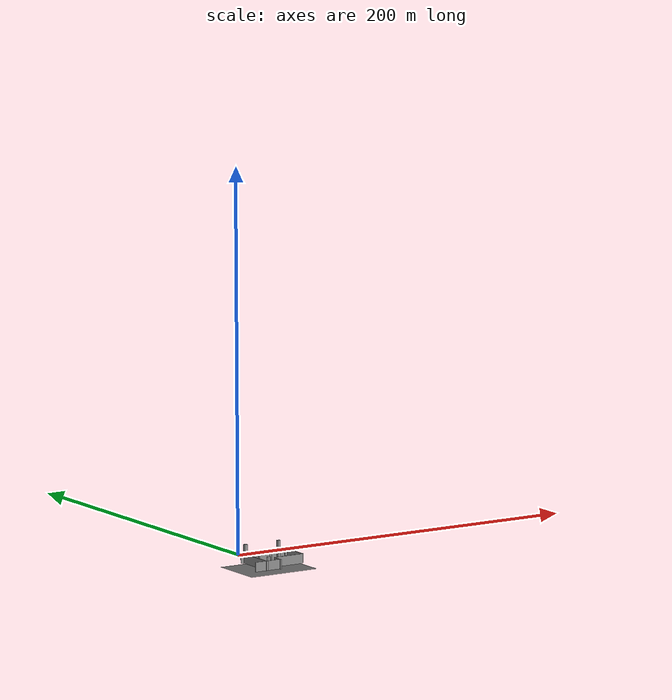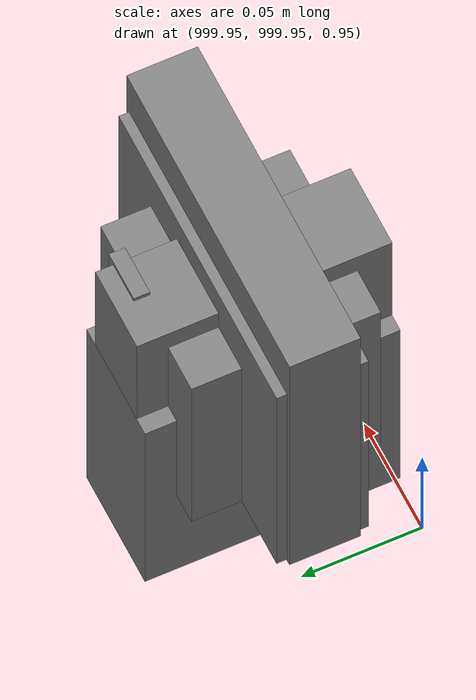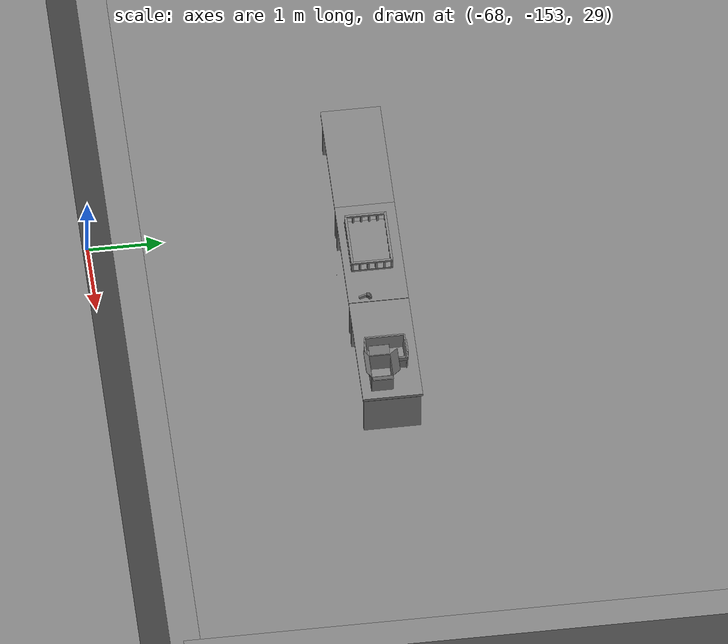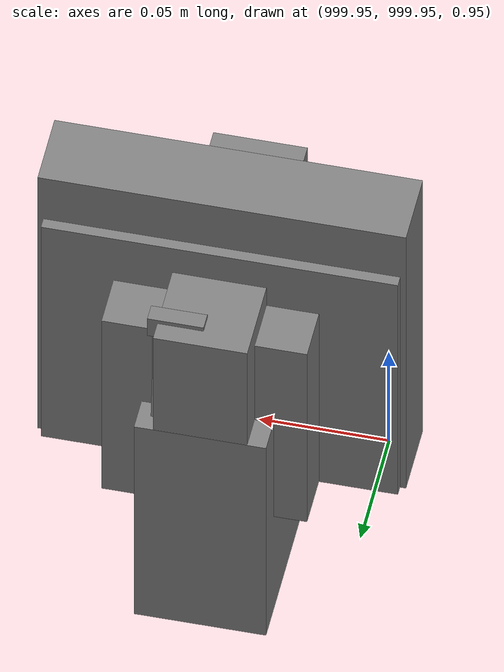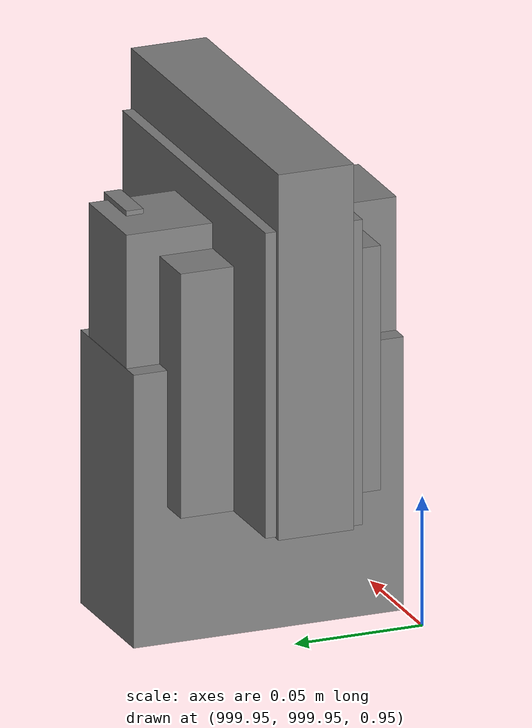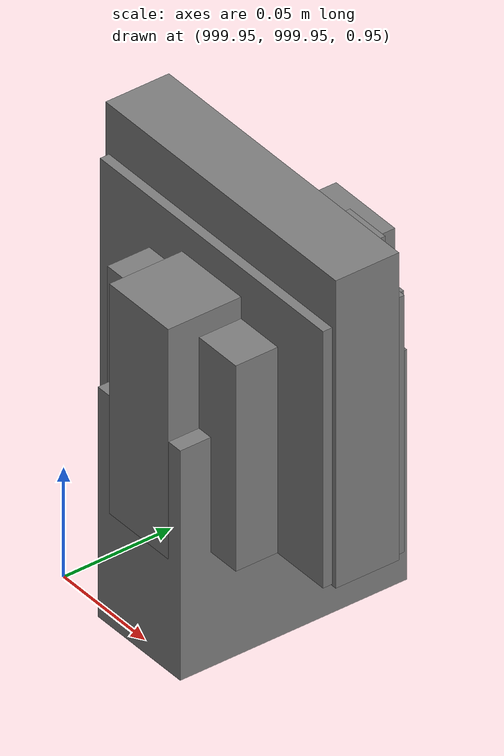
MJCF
<mujoco>
    <option gravity="0.000000000 0.000000000 -9.810000420" timestep="0.0049999999" integrator="implicitfast" density="1.225" viscosity="1.8000001e-05" noslip_iterations="10" iterations="100" sdf_iterations="50">
        <flag multiccd="disable"/>
    </option>
    <size memory="1000M"/>
    <compiler coordinate="local"/>
    <worldbody>
        <light cutoff="30" pos="0 1 1" dir="0 -1 -2"/>
        <light cutoff="30" pos="0 -1 1" dir="0 1 -2"/>
        <body pos="-64.866622925 -149.383972168 30.183746338" euler="89.999984741 89.999946594 0.000000000" name="openloong_gripper_2f85_fix_base_usda_bluebox_01">
            <geom contype="1" conaffinity="1" density="1000" type="box" material="" rgba="0.500000000 0.500000000 0.500000000 1.000000000" solimp="0.899999976 0.949999988 0.001000000" friction="1.000000000 0.005000000 0.000100000" solref="0.020000000 1.000000000" margin="0" condim="3" group="0" pos="0.276580811 0.187225342 0.000068665" quat="0.707106948 0.000077471 0.707106352 0.000077486" size="0.100000001 0.057999998 0.010000000" name="openloong_gripper_2f85_fix_base_usda_geom_37E6BAEB_CBDF_4380_BDBA_09B5BDBDC5F6"/>
            <geom contype="1" conaffinity="1" density="1000" type="box" material="" rgba="0.500000000 0.500000000 0.500000000 1.000000000" solimp="0.899999976 0.949999988 0.001000000" friction="1.000000000 0.005000000 0.000100000" solref="0.020000000 1.000000000" margin="0" condim="3" group="0" pos="0.000000000 0.002883911 0.000000000" quat="0.999999881 0.000000000 0.000000000 0.000000000" size="0.254000008 0.003000000 0.172000006" name="openloong_gripper_2f85_fix_base_usda_geom_35DA73F0_0263_4F3C_9F69_5748591F8C5D"/>
            <geom contype="1" conaffinity="1" density="1000" type="box" material="" rgba="0.500000000 0.500000000 0.500000000 1.000000000" solimp="0.899999976 0.949999988 0.001000000" friction="1.000000000 0.005000000 0.000100000" solref="0.020000000 1.000000000" margin="0" condim="3" group="0" pos="0.000000000 0.124874115 0.173484802" quat="0.999796331 0.020176515 -0.000000015 0.000000030" size="0.259999990 0.119999997 0.007000000" name="openloong_gripper_2f85_fix_base_usda_geom_0391FE30_E96F_44D2_9FDD_2842561F3F9D"/>
            <geom contype="1" conaffinity="1" density="1000" type="box" material="" rgba="0.500000000 0.500000000 0.500000000 1.000000000" solimp="0.899999976 0.949999988 0.001000000" friction="1.000000000 0.005000000 0.000100000" solref="0.020000000 1.000000000" margin="0" condim="3" group="0" pos="0.000000000 0.124874115 -0.173469543" quat="0.999796331 -0.020176545 -0.000000015 0.000000000" size="0.259999990 0.119999997 0.007000000" name="openloong_gripper_2f85_fix_base_usda_geom_3E7A9967_F854_4669_B7DF_84BF046A4A96"/>
            <geom contype="1" conaffinity="1" density="1000" type="box" material="" rgba="0.500000000 0.500000000 0.500000000 1.000000000" solimp="0.899999976 0.949999988 0.001000000" friction="1.000000000 0.005000000 0.000100000" solref="0.020000000 1.000000000" margin="0" condim="3" group="0" pos="0.000000000 0.214008331 0.188980103" quat="0.999912977 0.013176724 0.000000015 0.000000000" size="0.259999990 0.029999999 0.012500000" name="openloong_gripper_2f85_fix_base_usda_geom_0A90C8CD_5ACB_450C_8AEB_36A6531943ED"/>
            <geom contype="1" conaffinity="1" density="1000" type="box" material="" rgba="0.500000000 0.500000000 0.500000000 1.000000000" solimp="0.899999976 0.949999988 0.001000000" friction="1.000000000 0.005000000 0.000100000" solref="0.020000000 1.000000000" margin="0" condim="3" group="0" pos="-0.258361816 0.125289917 0.001876831" quat="0.702796936 -0.020792112 0.710783124 0.020769298" size="0.189999998 0.119999997 0.009000000" name="openloong_gripper_2f85_fix_base_usda_geom_635C979D_C585_4B08_ABFD_76EDF8CD342D"/>
            <geom contype="1" conaffinity="1" density="1000" type="box" material="" rgba="0.500000000 0.500000000 0.500000000 1.000000000" solimp="0.899999976 0.949999988 0.001000000" friction="1.000000000 0.005000000 0.000100000" solref="0.020000000 1.000000000" margin="0" condim="3" group="0" pos="0.000000000 0.214008331 -0.188980103" quat="0.999912977 -0.013176769 0.000000030 0.000000015" size="0.259999990 0.029999999 0.012500000" name="openloong_gripper_2f85_fix_base_usda_geom_AEC4B685_E224_4839_B950_AEAA20905B6C"/>
            <geom contype="1" conaffinity="1" density="1000" type="box" material="" rgba="0.500000000 0.500000000 0.500000000 1.000000000" solimp="0.899999976 0.949999988 0.001000000" friction="1.000000000 0.005000000 0.000100000" solref="0.020000000 1.000000000" margin="0" condim="3" group="0" pos="-0.276611328 0.187225342 0.000068665" quat="0.707106650 0.000077441 0.707106709 0.000077456" size="0.100000001 0.057999998 0.010000000" name="openloong_gripper_2f85_fix_base_usda_geom_15954228_3277_49F4_825C_2EB04FEAA10E"/>
            <geom contype="1" conaffinity="1" density="1000" type="box" material="" rgba="0.500000000 0.500000000 0.500000000 1.000000000" solimp="0.899999976 0.949999988 0.001000000" friction="1.000000000 0.005000000 0.000100000" solref="0.020000000 1.000000000" margin="0" condim="3" group="0" pos="0.258331299 0.125289917 0.001876831" quat="0.702851415 0.018856421 0.710823774 -0.019329369" size="0.189999998 0.119999997 0.009000000" name="openloong_gripper_2f85_fix_base_usda_geom_57440ECE_30E0_4F75_A02B_C6BB18066166"/>
            <freejoint name="openloong_gripper_2f85_fix_base_usda_bluebox_01_joint"/>
            <site size="0.005000000 0.005000000 0.005000000" rgba="0.500000000 0.500000000 0.500000000 1.000000000" pos="0.000000000 0.000000000 0.000000000" quat="0.999961913 0.008726534 0.000000000 0.000000000" group="0" type="sphere" name="openloong_gripper_2f85_fix_base_usda_bluebox_01site"/>
        </body>
        <body pos="-64.496299744 -149.491867065 30.235729218" euler="0.000000000 0.000000000 89.999946594" name="openloong_gripper_2f85_fix_base_usda_cardboardbox_01">
            <geom contype="1" conaffinity="1" density="1000" type="box" material="" rgba="0.500000000 0.500000000 0.500000000 1.000000000" solimp="0.899999976 0.949999988 0.001000000" friction="1.000000000 0.005000000 0.000100000" solref="0.020000000 1.000000000" margin="0" condim="3" group="0" pos="-0.003166199 -0.004086494 0.005052090" quat="1.000000000 0.000000000 0.000000000 0.000000000" size="0.142499998 0.177500010 0.005000000" name="openloong_gripper_2f85_fix_base_usda_geom_2AA0A221_98C2_470F_A9C0_0518A9D05928"/>
            <geom contype="1" conaffinity="1" density="1000" type="box" material="" rgba="0.500000000 0.500000000 0.500000000 1.000000000" solimp="0.899999976 0.949999988 0.001000000" friction="1.000000000 0.005000000 0.000100000" solref="0.020000000 1.000000000" margin="0" condim="3" group="0" pos="-0.003166199 0.170316696 0.150570869" quat="1.000000000 0.000000000 0.000000000 0.000000000" size="0.142499998 0.005000000 0.149999991" name="openloong_gripper_2f85_fix_base_usda_geom_C2588705_0157_4800_94AE_647754E010A6"/>
            <geom contype="1" conaffinity="1" density="1000" type="box" material="" rgba="0.500000000 0.500000000 0.500000000 1.000000000" solimp="0.899999976 0.949999988 0.001000000" friction="1.000000000 0.005000000 0.000100000" solref="0.020000000 1.000000000" margin="0" condim="3" group="0" pos="-0.147399902 -0.005307198 0.150570869" quat="1.000000000 0.000000000 0.000000000 0.000000000" size="0.005000000 0.177500010 0.149999991" name="openloong_gripper_2f85_fix_base_usda_geom_104EDF1E_FFE8_4EE0_AC0E_46B83D4843DE"/>
            <geom contype="1" conaffinity="1" density="1000" type="box" material="" rgba="0.500000000 0.500000000 0.500000000 1.000000000" solimp="0.899999976 0.949999988 0.001000000" friction="1.000000000 0.005000000 0.000100000" solref="0.020000000 1.000000000" margin="0" condim="3" group="0" pos="0.140275955 -0.005307198 0.150570869" quat="1.000000000 0.000000000 0.000000000 0.000000000" size="0.005000000 0.177500010 0.149999991" name="openloong_gripper_2f85_fix_base_usda_geom_2ABC5CE9_E7DD_4432_98B5_77ECE29E7382"/>
            <geom contype="1" conaffinity="1" density="1000" type="box" material="" rgba="0.500000000 0.500000000 0.500000000 1.000000000" solimp="0.899999976 0.949999988 0.001000000" friction="1.000000000 0.005000000 0.000100000" solref="0.020000000 1.000000000" margin="0" condim="3" group="0" pos="-0.003166199 -0.181550980 0.150570869" quat="1.000000000 0.000000000 0.000000000 0.000000000" size="0.142499998 0.005000000 0.149999991" name="openloong_gripper_2f85_fix_base_usda_geom_3C17265D_EC1B_410E_80AA_D3DB5A44BBB9"/>
            <freejoint name="openloong_gripper_2f85_fix_base_usda_cardboardbox_01_joint"/>
            <site size="0.005000000 0.005000000 0.005000000" rgba="0.500000000 0.500000000 0.500000000 1.000000000" pos="0.000000000 0.000000000 0.000000000" quat="0.999961913 0.008726535 0.000000000 0.000000000" group="0" type="sphere" name="openloong_gripper_2f85_fix_base_usda_site_2BDF3E68_A2B5_4FC4_8CDC_1E8F67666B8C"/>
            <body pos="0.139160156 -0.004048347 0.301930904" euler="-179.999954224 49.383502960 179.999954224" name="openloong_gripper_2f85_fix_base_usda_A1_006">
                <geom contype="1" conaffinity="1" density="1000" type="box" material="" rgba="0.500000000 0.500000000 0.500000000 1.000000000" solimp="0.899999976 0.949999988 0.001000000" friction="1.000000000 0.005000000 0.000100000" solref="0.020000000 1.000000000" margin="0" condim="3" group="0" pos="-0.071587563 0.000009537 0.001745224" quat="0.999999881 0.000000000 0.000000000 0.000000000" size="0.071249999 0.179999992 0.002500000" name="openloong_gripper_2f85_fix_base_usda_geom_12CAEE19_836F_4041_9398_E1BAC21F9DD8"/>
                <joint armature="0" stiffness="0.07" damping="0.0099999998" axis="0.000000 1.000000 0.000000" type="hinge" name="openloong_gripper_2f85_fix_base_usda_A1_006"/>
            </body>
            <body pos="-0.145902634 -0.004086494 0.301938057" euler="-180.000000000 -60.000011444 -180.000000000" name="openloong_gripper_2f85_fix_base_usda_A2_006">
                <geom contype="1" conaffinity="1" density="1000" type="box" material="" rgba="0.500000000 0.500000000 0.500000000 1.000000000" solimp="0.899999976 0.949999988 0.001000000" friction="1.000000000 0.005000000 0.000100000" solref="0.020000000 1.000000000" margin="0" condim="3" group="0" pos="0.071268082 0.000009537 0.002717972" quat="0.000002921 0.000000000 -0.000000030 0.999999881" size="0.071249999 0.179999992 0.002500000" name="openloong_gripper_2f85_fix_base_usda_geom_A3D0B663_8CD6_4D97_A497_05AEFF41F998"/>
                <joint armature="0" stiffness="0.07" damping="0.0099999998" axis="0.000000 1.000000 0.000000" type="hinge" name="openloong_gripper_2f85_fix_base_usda_A2_006"/>
            </body>
            <body pos="-0.003385544 0.175991058 0.301930904" euler="-125.858116150 -0.000004561 0.000002331" name="openloong_gripper_2f85_fix_base_usda_B2_006">
                <geom contype="1" conaffinity="1" density="1000" type="box" material="" rgba="0.500000000 0.500000000 0.500000000 1.000000000" solimp="0.899999976 0.949999988 0.001000000" friction="1.000000000 0.005000000 0.000100000" solref="0.020000000 1.000000000" margin="0" condim="3" group="0" pos="0.000009537 -0.070939064 -0.002470016" quat="0.999614120 0.027776197 -0.000000015 0.000000030" size="0.137500003 0.064999998 0.005000000" name="openloong_gripper_2f85_fix_base_usda_geom_1EC9307D_0305_4858_97A4_82EFBEF7CDC5"/>
                <joint armature="0" stiffness="0.07" damping="0.0099999998" axis="1.000000 0.000000 0.000000" type="hinge" name="openloong_gripper_2f85_fix_base_usda_B2_006"/>
            </body>
            <body pos="-0.003385544 -0.184140205 0.301938057" euler="147.805557251 0.000000000 0.000000000" name="openloong_gripper_2f85_fix_base_usda_B1_006">
                <geom contype="1" conaffinity="1" density="1000" type="box" material="" rgba="0.500000000 0.500000000 0.500000000 1.000000000" solimp="0.899999976 0.949999988 0.001000000" friction="1.000000000 0.005000000 0.000100000" solref="0.020000000 1.000000000" margin="0" condim="3" group="0" pos="-0.000028610 0.070202351 -0.002703667" quat="0.999614179 -0.027776167 0.000000000 0.000000000" size="0.137500003 0.064999998 0.005000000" name="openloong_gripper_2f85_fix_base_usda_geom_FFF52B18_F008_4559_89AE_F0813DAB0171"/>
                <joint armature="0" stiffness="0.07" damping="0.0099999998" axis="1.000000 0.000000 0.000000" type="hinge" name="openloong_gripper_2f85_fix_base_usda_B1_006"/>
            </body>
        </body>
        <body pos="-65.882858276 -149.481979370 30.229999542" euler="-64.487716675 0.000000000 0.000000000" name="openloong_gripper_2f85_fix_base_usda_Barcode">
            <geom contype="1" conaffinity="1" density="1000" type="box" material="" rgba="0.500000000 0.500000000 0.500000000 1.000000000" solimp="0.899999976 0.949999988 0.001000000" friction="1.000000000 0.005000000 0.000100000" solref="0.020000000 1.000000000" margin="0" condim="3" group="0" pos="0.000000000 0.013038635 0.001419067" quat="0.000000000 0.000000000 0.000000000 1.000000119" size="0.034000002 0.010000000 0.017999999" name="openloong_gripper_2f85_fix_base_usda_geom_AECF214F_87D8_4338_A6A4_9C35E1E7F9D4"/>
            <geom contype="1" conaffinity="1" density="1000" type="box" material="" rgba="0.500000000 0.500000000 0.500000000 1.000000000" solimp="0.899999976 0.949999988 0.001000000" friction="1.000000000 0.005000000 0.000100000" solref="0.020000000 1.000000000" margin="0" condim="3" group="0" pos="0.000000000 -0.035301208 -0.007095337" quat="0.000000000 0.000000000 -0.043619365 0.999048233" size="0.028999999 0.010000000 0.020000000" name="openloong_gripper_2f85_fix_base_usda_geom_1E32E908_24E9_49F1_8606_01246C446493"/>
            <geom contype="1" conaffinity="1" density="1000" type="box" material="" rgba="0.500000000 0.500000000 0.500000000 1.000000000" solimp="0.899999976 0.949999988 0.001000000" friction="1.000000000 0.005000000 0.000100000" solref="0.020000000 1.000000000" margin="0" condim="3" group="0" pos="0.000000000 -0.043411255 -0.011749268" quat="0.922262907 0.386563420 0.000000000 0.000000000" size="0.026000001 0.010000000 0.020000000" name="openloong_gripper_2f85_fix_base_usda_geom_41BC8551_B9F1_4BA2_BD16_DF5545FD7CAE"/>
            <geom contype="1" conaffinity="1" density="1000" type="box" material="" rgba="0.500000000 0.500000000 0.500000000 1.000000000" solimp="0.899999976 0.949999988 0.001000000" friction="1.000000000 0.005000000 0.000100000" solref="0.020000000 1.000000000" margin="0" condim="3" group="0" pos="0.000000000 -0.016967773 -0.031860352" quat="0.000000000 0.000000000 0.000000000 1.000000119" size="0.008000000 0.010000000 0.013000000" name="openloong_gripper_2f85_fix_base_usda_geom_F7ACAE24_EB50_476F_BDDA_5A4B3653E599"/>
            <geom contype="1" conaffinity="1" density="1000" type="box" material="" rgba="0.500000000 0.500000000 0.500000000 1.000000000" solimp="0.899999976 0.949999988 0.001000000" friction="1.000000000 0.005000000 0.000100000" solref="0.020000000 1.000000000" margin="0" condim="3" group="0" pos="0.000000000 -0.001869202 0.000312805" quat="0.953716993 0.300705761 0.000000000 0.000000000" size="0.032000002 0.010000000 0.018999999" name="openloong_gripper_2f85_fix_base_usda_geom_4E0C86AA_3754_409A_8A04_812E468C18A3"/>
            <geom contype="1" conaffinity="1" density="1000" type="box" material="" rgba="0.500000000 0.500000000 0.500000000 1.000000000" solimp="0.899999976 0.949999988 0.001000000" friction="1.000000000 0.005000000 0.000100000" solref="0.020000000 1.000000000" margin="0" condim="3" group="0" pos="0.000000000 -0.019531250 -0.003173828" quat="0.953716993 0.300705761 0.000000000 0.000000000" size="0.030999999 0.010000000 0.020000000" name="openloong_gripper_2f85_fix_base_usda_geom_10537352_8739_4BDC_AE86_9EF8340B4D44"/>
            <geom contype="1" conaffinity="1" density="1000" type="box" material="" rgba="0.500000000 0.500000000 0.500000000 1.000000000" solimp="0.899999976 0.949999988 0.001000000" friction="1.000000000 0.005000000 0.000100000" solref="0.020000000 1.000000000" margin="0" condim="3" group="0" pos="0.000000000 -0.035301208 -0.007095337" quat="0.953716993 0.300705761 0.000000000 0.000000000" size="0.028999999 0.010000000 0.020000000" name="openloong_gripper_2f85_fix_base_usda_geom_394CE063_1447_471C_B583_BD43C5C53B95"/>
            <geom contype="1" conaffinity="1" density="1000" type="box" material="" rgba="0.500000000 0.500000000 0.500000000 1.000000000" solimp="0.899999976 0.949999988 0.001000000" friction="1.000000000 0.005000000 0.000100000" solref="0.020000000 1.000000000" margin="0" condim="3" group="0" pos="0.000000000 -0.042617798 -0.071121216" quat="0.000000000 0.000000000 0.000000000 1.000000119" size="0.013000000 0.021000000 0.059999999" name="openloong_gripper_2f85_fix_base_usda_geom_590A5360_3EE9_4949_A94D_D944AC797AA9"/>
            <freejoint name="openloong_gripper_2f85_fix_base_usda_Barcode_joint"/>
            <site size="0.005000000 0.005000000 0.005000000" rgba="0.500000000 0.500000000 0.500000000 1.000000000" pos="0.000000000 0.000000000 0.000000000" quat="1.000000000 0.000000000 0.000000000 0.000000000" group="0" type="sphere" name="openloong_gripper_2f85_fix_base_usda_Barcode_site"/>
        </body>
        <body pos="-66.745018005 -149.392349243 30.184000015" euler="0.000000000 0.000000000 89.999946594" name="[22331504624607]_Basket_01">
            <geom contype="1" conaffinity="1" density="1000" type="box" material="" rgba="0.500000000 0.500000000 0.500000000 1.000000000" solimp="0.899999976 0.949999988 0.001000000" friction="1.000000000 0.005000000 0.000100000" solref="0.020000000 1.000000000" margin="0" condim="3" group="0" pos="-0.052425385 0.389207840 0.089787483" quat="0.707107008 0.000000000 0.000000000 0.707106411" size="0.014249999 0.014249999 0.059999999" name="[22331504624607]_geom_CC03943A_34EF_4EE6_AD69_3F439D2CA3B8"/>
            <geom contype="1" conaffinity="1" density="1000" type="box" material="" rgba="0.500000000 0.500000000 0.500000000 1.000000000" solimp="0.899999976 0.949999988 0.001000000" friction="1.000000000 0.005000000 0.000100000" solref="0.020000000 1.000000000" margin="0" condim="3" group="0" pos="0.264015198 -0.133043289 0.089787483" quat="0.707107008 0.000000000 0.000000000 0.707106411" size="0.014249999 0.014249999 0.059999999" name="[22331504624607]_geom_03501043_1CF4_4569_B6FB_194DBF0514A9"/>
            <geom contype="1" conaffinity="1" density="1000" type="box" material="" rgba="0.500000000 0.500000000 0.500000000 1.000000000" solimp="0.899999976 0.949999988 0.001000000" friction="1.000000000 0.005000000 0.000100000" solref="0.020000000 1.000000000" margin="0" condim="3" group="0" pos="-0.264015198 -0.265548706 0.089793205" quat="0.707107008 0.000000000 0.000000000 0.707106411" size="0.014249999 0.014249999 0.059999999" name="[22331504624607]_geom_0B5063FA_9B9A_4CD0_946A_1C826CD3F353"/>
            <geom contype="1" conaffinity="1" density="1000" type="box" material="" rgba="0.500000000 0.500000000 0.500000000 1.000000000" solimp="0.899999976 0.949999988 0.001000000" friction="1.000000000 0.005000000 0.000100000" solref="0.020000000 1.000000000" margin="0" condim="3" group="0" pos="-0.160263062 -0.389322281 0.089793205" quat="0.707107008 0.000000000 0.000000000 0.707106411" size="0.014249999 0.014249999 0.059999999" name="[22331504624607]_geom_5270251D_9BE5_455D_9F15_1658DBAC9921"/>
            <geom contype="1" conaffinity="1" density="1000" type="box" material="" rgba="0.500000000 0.500000000 0.500000000 1.000000000" solimp="0.899999976 0.949999988 0.001000000" friction="1.000000000 0.005000000 0.000100000" solref="0.020000000 1.000000000" margin="0" condim="3" group="0" pos="0.162265778 -0.389322281 0.089787483" quat="0.707107008 0.000000000 0.000000000 0.707106411" size="0.014249999 0.014249999 0.059999999" name="[22331504624607]_geom_D72BE778_D95B_43F8_8A40_A121ADB7B53B"/>
            <geom contype="1" conaffinity="1" density="1000" type="box" material="" rgba="0.500000000 0.500000000 0.500000000 1.000000000" solimp="0.899999976 0.949999988 0.001000000" friction="1.000000000 0.005000000 0.000100000" solref="0.020000000 1.000000000" margin="0" condim="3" group="0" pos="0.264015198 0.389207840 0.089787483" quat="0.707107008 0.000000000 0.000000000 0.707106411" size="0.014249999 0.014249999 0.059999999" name="[22331504624607]_geom_A240BD1E_4481_45EB_83F3_68FEB7B25598"/>
            <geom contype="1" conaffinity="1" density="1000" type="box" material="" rgba="0.500000000 0.500000000 0.500000000 1.000000000" solimp="0.899999976 0.949999988 0.001000000" friction="1.000000000 0.005000000 0.000100000" solref="0.020000000 1.000000000" margin="0" condim="3" group="0" pos="-0.264015198 -0.133043289 0.089793205" quat="0.707107008 0.000000000 0.000000000 0.707106411" size="0.014249999 0.014249999 0.059999999" name="[22331504624607]_geom_4D038D7D_16C0_4B22_B17B_006FF9B9C096"/>
            <geom contype="1" conaffinity="1" density="1000" type="box" material="" rgba="0.500000000 0.500000000 0.500000000 1.000000000" solimp="0.899999976 0.949999988 0.001000000" friction="1.000000000 0.005000000 0.000100000" solref="0.020000000 1.000000000" margin="0" condim="3" group="0" pos="-0.264026642 0.269256592 0.089793205" quat="0.707107008 0.000000000 0.000000000 0.707106411" size="0.014249999 0.014249999 0.059999999" name="[22331504624607]_geom_984C510F_8577_482A_B09C_BC08565065A6"/>
            <geom contype="1" conaffinity="1" density="1000" type="box" material="" rgba="0.500000000 0.500000000 0.500000000 1.000000000" solimp="0.899999976 0.949999988 0.001000000" friction="1.000000000 0.005000000 0.000100000" solref="0.020000000 1.000000000" margin="0" condim="3" group="0" pos="0.054462433 0.389207840 0.089787483" quat="0.707107008 0.000000000 0.000000000 0.707106411" size="0.014249999 0.014249999 0.059999999" name="[22331504624607]_geom_500FAE0F_43FF_4C65_B896_9DD65B063853"/>
            <geom contype="1" conaffinity="1" density="1000" type="box" material="" rgba="0.500000000 0.500000000 0.500000000 1.000000000" solimp="0.899999976 0.949999988 0.001000000" friction="1.000000000 0.005000000 0.000100000" solref="0.020000000 1.000000000" margin="0" condim="3" group="0" pos="0.054462433 -0.389322281 0.089787483" quat="0.707107008 0.000000000 0.000000000 0.707106411" size="0.014249999 0.014249999 0.059999999" name="[22331504624607]_geom_49AAA0F2_F683_4E13_8544_F78DD2B9C0AD"/>
            <geom contype="1" conaffinity="1" density="1000" type="box" material="" rgba="0.500000000 0.500000000 0.500000000 1.000000000" solimp="0.899999976 0.949999988 0.001000000" friction="1.000000000 0.005000000 0.000100000" solref="0.020000000 1.000000000" margin="0" condim="3" group="0" pos="0.264015198 0.269256592 0.089793205" quat="0.707107008 0.000000000 0.000000000 0.707106411" size="0.014249999 0.014249999 0.059999999" name="[22331504624607]_geom_E1529D74_7BA6_4CB1_B4D7_BC8601F55163"/>
            <geom contype="1" conaffinity="1" density="1000" type="box" material="" rgba="0.500000000 0.500000000 0.500000000 1.000000000" solimp="0.899999976 0.949999988 0.001000000" friction="1.000000000 0.005000000 0.000100000" solref="0.020000000 1.000000000" margin="0" condim="3" group="0" pos="0.264015198 -0.389322281 0.089787483" quat="0.707107008 0.000000000 0.000000000 0.707106411" size="0.014249999 0.014249999 0.059999999" name="[22331504624607]_geom_C48C7F40_D7D5_472D_A432_F2946E05E98F"/>
            <geom contype="1" conaffinity="1" density="1000" type="box" material="" rgba="0.500000000 0.500000000 0.500000000 1.000000000" solimp="0.899999976 0.949999988 0.001000000" friction="1.000000000 0.005000000 0.000100000" solref="0.020000000 1.000000000" margin="0" condim="3" group="0" pos="0.000000000 0.000000000 0.015998840" quat="0.707107008 0.000000000 0.000000000 0.707106411" size="0.403499991 0.279000014 0.015750000" name="[22331504624607]_geom_A6032BDE_9502_43B4_BE8B_AB427608707B"/>
            <geom contype="1" conaffinity="1" density="1000" type="box" material="" rgba="0.500000000 0.500000000 0.500000000 1.000000000" solimp="0.899999976 0.949999988 0.001000000" friction="1.000000000 0.005000000 0.000100000" solref="0.020000000 1.000000000" margin="0" condim="3" group="0" pos="0.000000000 -0.389476776 0.163619041" quat="0.707107008 0.000000000 0.000000000 0.707106411" size="0.015000000 0.277500004 0.015750000" name="[22331504624607]_geom_3330BDFF_0A4E_477B_B429_2EE14163D211"/>
            <geom contype="1" conaffinity="1" density="1000" type="box" material="" rgba="0.500000000 0.500000000 0.500000000 1.000000000" solimp="0.899999976 0.949999988 0.001000000" friction="1.000000000 0.005000000 0.000100000" solref="0.020000000 1.000000000" margin="0" condim="3" group="0" pos="0.162265778 0.389207840 0.089787483" quat="0.707107008 0.000000000 0.000000000 0.707106411" size="0.014249999 0.014249999 0.059999999" name="[22331504624607]_geom_31FC5AD2_2D23_425B_B0E4_9BBE10B40F57"/>
            <geom contype="1" conaffinity="1" density="1000" type="box" material="" rgba="0.500000000 0.500000000 0.500000000 1.000000000" solimp="0.899999976 0.949999988 0.001000000" friction="1.000000000 0.005000000 0.000100000" solref="0.020000000 1.000000000" margin="0" condim="3" group="0" pos="0.000000000 0.389471054 0.163619041" quat="0.707107008 0.000000000 0.000000000 0.707106411" size="0.015000000 0.277500004 0.015750000" name="[22331504624607]_geom_BE54D3F4_B377_4126_AFA3_E48E599EBC18"/>
            <geom contype="1" conaffinity="1" density="1000" type="box" material="" rgba="0.500000000 0.500000000 0.500000000 1.000000000" solimp="0.899999976 0.949999988 0.001000000" friction="1.000000000 0.005000000 0.000100000" solref="0.020000000 1.000000000" margin="0" condim="3" group="0" pos="-0.263511658 0.000000000 0.163619041" quat="0.707107008 0.000000000 0.000000000 0.707106411" size="0.403499991 0.015000000 0.015750000" name="[22331504624607]_geom_C049CE6D_2010_4694_8471_2AD6791F71D8"/>
            <geom contype="1" conaffinity="1" density="1000" type="box" material="" rgba="0.500000000 0.500000000 0.500000000 1.000000000" solimp="0.899999976 0.949999988 0.001000000" friction="1.000000000 0.005000000 0.000100000" solref="0.020000000 1.000000000" margin="0" condim="3" group="0" pos="-0.264015198 0.141334534 0.089793205" quat="0.707107008 0.000000000 0.000000000 0.707106411" size="0.014249999 0.014249999 0.059999999" name="[22331504624607]_geom_AEA0A715_126F_42EA_82DD_EF44FF35F762"/>
            <geom contype="1" conaffinity="1" density="1000" type="box" material="" rgba="0.500000000 0.500000000 0.500000000 1.000000000" solimp="0.899999976 0.949999988 0.001000000" friction="1.000000000 0.005000000 0.000100000" solref="0.020000000 1.000000000" margin="0" condim="3" group="0" pos="0.264015198 -0.265548706 0.089787483" quat="0.707107008 0.000000000 0.000000000 0.707106411" size="0.014249999 0.014249999 0.059999999" name="[22331504624607]_geom_6A97215C_23B7_4421_952C_9505B4FC1A66"/>
            <geom contype="1" conaffinity="1" density="1000" type="box" material="" rgba="0.500000000 0.500000000 0.500000000 1.000000000" solimp="0.899999976 0.949999988 0.001000000" friction="1.000000000 0.005000000 0.000100000" solref="0.020000000 1.000000000" margin="0" condim="3" group="0" pos="-0.160263062 0.389207840 0.089787483" quat="0.707107008 0.000000000 0.000000000 0.707106411" size="0.014249999 0.014249999 0.059999999" name="[22331504624607]_geom_8567D99F_83D9_4A55_BD6A_B5EEADD71263"/>
            <geom contype="1" conaffinity="1" density="1000" type="box" material="" rgba="0.500000000 0.500000000 0.500000000 1.000000000" solimp="0.899999976 0.949999988 0.001000000" friction="1.000000000 0.005000000 0.000100000" solref="0.020000000 1.000000000" margin="0" condim="3" group="0" pos="-0.052425385 -0.389322281 0.089787483" quat="0.707107008 0.000000000 0.000000000 0.707106411" size="0.014249999 0.014249999 0.059999999" name="[22331504624607]_geom_0F6ABC4D_E551_4B28_96F9_A297655DE59A"/>
            <geom contype="1" conaffinity="1" density="1000" type="box" material="" rgba="0.500000000 0.500000000 0.500000000 1.000000000" solimp="0.899999976 0.949999988 0.001000000" friction="1.000000000 0.005000000 0.000100000" solref="0.020000000 1.000000000" margin="0" condim="3" group="0" pos="-0.264026642 -0.389322281 0.089793205" quat="0.707107008 0.000000000 0.000000000 0.707106411" size="0.014249999 0.014249999 0.059999999" name="[22331504624607]_geom_30A6428C_01D5_457B_B804_3FD562863DB1"/>
            <geom contype="1" conaffinity="1" density="1000" type="box" material="" rgba="0.500000000 0.500000000 0.500000000 1.000000000" solimp="0.899999976 0.949999988 0.001000000" friction="1.000000000 0.005000000 0.000100000" solref="0.020000000 1.000000000" margin="0" condim="3" group="0" pos="0.264015198 0.141334534 0.089787483" quat="0.707107008 0.000000000 0.000000000 0.707106411" size="0.014249999 0.014249999 0.059999999" name="[22331504624607]_geom_8475D612_862F_4A22_B13B_871CA31C7F20"/>
            <geom contype="1" conaffinity="1" density="1000" type="box" material="" rgba="0.500000000 0.500000000 0.500000000 1.000000000" solimp="0.899999976 0.949999988 0.001000000" friction="1.000000000 0.005000000 0.000100000" solref="0.020000000 1.000000000" margin="0" condim="3" group="0" pos="-0.264015198 0.389207840 0.089793205" quat="0.707107008 0.000000000 0.000000000 0.707106411" size="0.014249999 0.014249999 0.059999999" name="[22331504624607]_geom_02EE5E9C_5D5B_44D5_BE1D_8857EBCE90FE"/>
            <geom contype="1" conaffinity="1" density="1000" type="box" material="" rgba="0.500000000 0.500000000 0.500000000 1.000000000" solimp="0.899999976 0.949999988 0.001000000" friction="1.000000000 0.005000000 0.000100000" solref="0.020000000 1.000000000" margin="0" condim="3" group="0" pos="0.264015198 0.004480362 0.089787483" quat="0.707107008 0.000000000 0.000000000 0.707106411" size="0.014249999 0.014249999 0.059999999" name="[22331504624607]_geom_C18937B5_6FEA_4EF7_BE46_8F273FB81842"/>
            <geom contype="1" conaffinity="1" density="1000" type="box" material="" rgba="0.500000000 0.500000000 0.500000000 1.000000000" solimp="0.899999976 0.949999988 0.001000000" friction="1.000000000 0.005000000 0.000100000" solref="0.020000000 1.000000000" margin="0" condim="3" group="0" pos="0.263694763 -0.000011444 0.163619041" quat="0.707107008 0.000000000 0.000000000 0.707106411" size="0.403499991 0.015000000 0.015750000" name="[22331504624607]_geom_DB8AAB84_6292_4416_AD70_01FCB8D6505C"/>
            <geom contype="1" conaffinity="1" density="1000" type="box" material="" rgba="0.500000000 0.500000000 0.500000000 1.000000000" solimp="0.899999976 0.949999988 0.001000000" friction="1.000000000 0.005000000 0.000100000" solref="0.020000000 1.000000000" margin="0" condim="3" group="0" pos="-0.264015198 0.004480362 0.089793205" quat="0.707107008 0.000000000 0.000000000 0.707106411" size="0.014249999 0.014249999 0.059999999" name="[22331504624607]_geom_9FD8E20F_BF56_486E_954B_5BEC03F61869"/>
            <freejoint name="[22331504624607]_joint_F219390A_E90E_402C_B631_86EB9A7380CC"/>
        </body>
        <body pos="0.000000000 0.000000000 0.000000000" euler="0.000000000 0.000000000 0.000000000" name="Static Objects_Static Objects">
            <geom contype="1" conaffinity="1" density="1000" type="box" material="" rgba="0.500000000 0.500000000 0.500000000 1.000000000" solimp="0.899999976 0.949999988 0.001000000" friction="1.000000000 0.005000000 0.000100000" solref="0.020000000 1.000000000" margin="0" condim="3" group="0" pos="-67.544113159 -149.365814209 29.727830887" quat="0.500000417 0.499999970 0.499999553 0.499999970" size="0.381000012 0.319999993 0.041000001" name="Static Objects_geom_31E4A04D_3FB0_4024_926E_A08ECEDFE3E9"/>
            <geom contype="1" conaffinity="1" density="1000" type="box" material="" rgba="0.500000000 0.500000000 0.500000000 1.000000000" solimp="0.899999976 0.949999988 0.001000000" friction="1.000000000 0.005000000 0.000100000" solref="0.020000000 1.000000000" margin="0" condim="3" group="0" pos="-68.239501953 -149.365814209 30.086868286" quat="0.500000417 0.499999970 0.499999553 0.499999970" size="0.370999992 0.039500002 0.745000005" name="Static Objects_geom_B871E500_5033_42A9_8B97_10A2F9802C3C"/>
            <geom contype="1" conaffinity="1" density="1000" type="box" material="" rgba="0.500000000 0.500000000 0.500000000 1.000000000" solimp="0.899999976 0.949999988 0.001000000" friction="1.000000000 0.005000000 0.000100000" solref="0.020000000 1.000000000" margin="0" condim="3" group="0" pos="-68.239501953 -149.365814209 30.147235870" quat="0.500000417 0.499999970 0.499999553 0.499999970" size="0.400000006 0.022000000 0.800000012" name="Static Objects_geom_C877ED26_C16D_49B0_A7FB_FE6258325072"/>
            <geom contype="1" conaffinity="1" density="1000" type="box" material="" rgba="0.500000000 0.500000000 0.500000000 1.000000000" solimp="0.899999976 0.949999988 0.001000000" friction="1.000000000 0.005000000 0.000100000" solref="0.020000000 1.000000000" margin="0" condim="3" group="0" pos="-68.934890747 -149.365814209 29.727830887" quat="0.500000417 0.499999970 0.499999553 0.499999970" size="0.381000012 0.319999993 0.041000001" name="Static Objects_geom_07E1D7A5_A0D9_42BC_AEEC_6DB600376866"/>
            <geom contype="1" conaffinity="1" density="1000" type="box" material="" rgba="0.500000000 0.500000000 0.500000000 1.000000000" solimp="0.899999976 0.949999988 0.001000000" friction="1.000000000 0.005000000 0.000100000" solref="0.020000000 1.000000000" margin="0" condim="3" group="0" pos="-68.239501953 -149.365814209 29.561563492" quat="0.500000417 0.499999970 0.499999553 0.499999970" size="0.020000000 0.022000000 0.660000026" name="Static Objects_geom_E0F36EB3_2FAA_4EA4_B96F_CE2C25476DFD"/>
            <geom contype="1" conaffinity="1" density="1000" type="box" material="" rgba="0.500000000 0.500000000 0.500000000 1.000000000" solimp="0.899999976 0.949999988 0.001000000" friction="1.000000000 0.005000000 0.000100000" solref="0.020000000 1.000000000" margin="0" condim="3" group="0" pos="-65.945671082 -149.365814209 29.727830887" quat="0.500000417 0.499999970 0.499999553 0.499999970" size="0.381000012 0.319999993 0.041000001" name="Static Objects_geom_EC872FDF_15C7_4D42_96BC_96CB2200DE60"/>
            <geom contype="1" conaffinity="1" density="1000" type="box" material="" rgba="0.500000000 0.500000000 0.500000000 1.000000000" solimp="0.899999976 0.949999988 0.001000000" friction="1.000000000 0.005000000 0.000100000" solref="0.020000000 1.000000000" margin="0" condim="3" group="0" pos="-66.641059875 -149.365814209 30.086868286" quat="0.500000417 0.499999970 0.499999553 0.499999970" size="0.370999992 0.039500002 0.745000005" name="Static Objects_geom_A223D769_46E5_4719_B1C6_4BDF7A1C8BA6"/>
            <geom contype="1" conaffinity="1" density="1000" type="box" material="" rgba="0.500000000 0.500000000 0.500000000 1.000000000" solimp="0.899999976 0.949999988 0.001000000" friction="1.000000000 0.005000000 0.000100000" solref="0.020000000 1.000000000" margin="0" condim="3" group="0" pos="-66.641059875 -149.365814209 30.147235870" quat="0.500000417 0.499999970 0.499999553 0.499999970" size="0.400000006 0.022000000 0.800000012" name="Static Objects_geom_B868BDDC_E378_4CE5_A422_3482D52D1B3B"/>
            <geom contype="1" conaffinity="1" density="1000" type="box" material="" rgba="0.500000000 0.500000000 0.500000000 1.000000000" solimp="0.899999976 0.949999988 0.001000000" friction="1.000000000 0.005000000 0.000100000" solref="0.020000000 1.000000000" margin="0" condim="3" group="0" pos="-67.336448669 -149.365814209 29.727830887" quat="0.500000417 0.499999970 0.499999553 0.499999970" size="0.381000012 0.319999993 0.041000001" name="Static Objects_geom_B1D60190_48B0_4709_8248_5292E4F30E66"/>
            <geom contype="1" conaffinity="1" density="1000" type="box" material="" rgba="0.500000000 0.500000000 0.500000000 1.000000000" solimp="0.899999976 0.949999988 0.001000000" friction="1.000000000 0.005000000 0.000100000" solref="0.020000000 1.000000000" margin="0" condim="3" group="0" pos="-66.641059875 -149.365814209 29.561563492" quat="0.500000417 0.499999970 0.499999553 0.499999970" size="0.020000000 0.022000000 0.660000026" name="Static Objects_geom_32FEE799_8787_4E6A_85E2_7CBA8AB8A96E"/>
            <geom contype="1" conaffinity="1" density="1000" type="box" material="" rgba="0.500000000 0.500000000 0.500000000 1.000000000" solimp="0.899999976 0.949999988 0.001000000" friction="1.000000000 0.005000000 0.000100000" solref="0.020000000 1.000000000" margin="0" condim="3" group="0" pos="-64.338577271 -149.365814209 29.727830887" quat="0.500000417 0.499999970 0.499999553 0.499999970" size="0.381000012 0.319999993 0.041000001" name="Static Objects_geom_266923AD_28CF_447A_BA7F_21A245DCE745"/>
            <geom contype="1" conaffinity="1" density="1000" type="box" material="" rgba="0.500000000 0.500000000 0.500000000 1.000000000" solimp="0.899999976 0.949999988 0.001000000" friction="1.000000000 0.005000000 0.000100000" solref="0.020000000 1.000000000" margin="0" condim="3" group="0" pos="-65.033966064 -149.365814209 30.086868286" quat="0.500000417 0.499999970 0.499999553 0.499999970" size="0.370999992 0.039500002 0.745000005" name="Static Objects_geom_9E3524A7_1880_4034_A5D2_E27BFA0133CE"/>
            <geom contype="1" conaffinity="1" density="1000" type="box" material="" rgba="0.500000000 0.500000000 0.500000000 1.000000000" solimp="0.899999976 0.949999988 0.001000000" friction="1.000000000 0.005000000 0.000100000" solref="0.020000000 1.000000000" margin="0" condim="3" group="0" pos="-65.033966064 -149.365814209 30.147235870" quat="0.500000417 0.499999970 0.499999553 0.499999970" size="0.400000006 0.022000000 0.800000012" name="Static Objects_geom_4944176B_10A6_41A4_9577_4DC8F22023E7"/>
            <geom contype="1" conaffinity="1" density="1000" type="box" material="" rgba="0.500000000 0.500000000 0.500000000 1.000000000" solimp="0.899999976 0.949999988 0.001000000" friction="1.000000000 0.005000000 0.000100000" solref="0.020000000 1.000000000" margin="0" condim="3" group="0" pos="-65.729354858 -149.365814209 29.727830887" quat="0.500000417 0.499999970 0.499999553 0.499999970" size="0.381000012 0.319999993 0.041000001" name="Static Objects_geom_8105B32A_D5E9_4E6E_805D_5512043DB29E"/>
            <geom contype="1" conaffinity="1" density="1000" type="box" material="" rgba="0.500000000 0.500000000 0.500000000 1.000000000" solimp="0.899999976 0.949999988 0.001000000" friction="1.000000000 0.005000000 0.000100000" solref="0.020000000 1.000000000" margin="0" condim="3" group="0" pos="-65.033966064 -149.365814209 29.561563492" quat="0.500000417 0.499999970 0.499999553 0.499999970" size="0.020000000 0.022000000 0.660000026" name="Static Objects_geom_87407C4D_BB6A_483A_B6D5_60F7B4E35A4B"/>
            <geom contype="1" conaffinity="1" density="1000" type="box" material="" rgba="0.500000000 0.500000000 0.500000000 1.000000000" solimp="0.899999976 0.949999988 0.001000000" friction="1.000000000 0.005000000 0.000100000" solref="0.020000000 1.000000000" margin="0" condim="3" group="0" pos="-61.754566193 -137.853729248 33.906845093" quat="0.707107067 0.000000000 0.000000000 0.707106471" size="0.759999990 0.759999990 4.500000000" name="Static Objects_geom_3DE11864_E9A6_4850_AA30_2B8A52AF411A"/>
            <geom contype="1" conaffinity="1" density="1000" type="box" material="" rgba="0.500000000 0.500000000 0.500000000 1.000000000" solimp="0.899999976 0.949999988 0.001000000" friction="1.000000000 0.005000000 0.000100000" solref="0.020000000 1.000000000" margin="0" condim="3" group="0" pos="-57.511135101 -144.927108765 31.707921982" quat="1.000000000 0.000000000 0.000000000 0.000000000" size="0.200000003 8.000000000 2.299999952" name="Static Objects_geom_4CCFE1DF_2CF5_4FF4_AADE_B136DC675CCF"/>
            <geom contype="1" conaffinity="1" density="1000" type="box" material="" rgba="0.500000000 0.500000000 0.500000000 1.000000000" solimp="0.899999976 0.949999988 0.001000000" friction="1.000000000 0.005000000 0.000100000" solref="0.020000000 1.000000000" margin="0" condim="3" group="0" pos="-80.517646790 -157.574050903 31.688196182" quat="0.707107067 0.000000000 0.000000000 0.707106471" size="0.600000024 0.600000024 2.299999952" name="Static Objects_geom_447CBA85_EE04_4DA4_B1DB_5CA1C6ECD51D"/>
            <geom contype="1" conaffinity="1" density="1000" type="box" material="" rgba="0.500000000 0.500000000 0.500000000 1.000000000" solimp="0.899999976 0.949999988 0.001000000" friction="1.000000000 0.005000000 0.000100000" solref="0.020000000 1.000000000" margin="0" condim="3" group="0" pos="-80.711044312 -147.414932251 31.666158676" quat="1.000000000 0.000000000 0.000000000 0.000000000" size="0.200000003 10.000000000 2.299999952" name="Static Objects_geom_81A349F8_11E7_4F82_8A57_2D271E9D3F1C"/>
            <geom contype="1" conaffinity="1" density="1000" type="box" material="" rgba="0.500000000 0.500000000 0.500000000 1.000000000" solimp="0.899999976 0.949999988 0.001000000" friction="1.000000000 0.005000000 0.000100000" solref="0.020000000 1.000000000" margin="0" condim="3" group="0" pos="-57.687217712 -137.434692383 31.688196182" quat="0.707107067 0.000000000 0.000000000 0.707106471" size="0.600000024 0.600000024 2.299999952" name="Static Objects_geom_63FEC5F7_12B6_465C_B517_7BB8790926DF"/>
            <geom contype="1" conaffinity="1" density="1000" type="box" material="" rgba="0.500000000 0.500000000 0.500000000 1.000000000" solimp="0.899999976 0.949999988 0.001000000" friction="1.000000000 0.005000000 0.000100000" solref="0.020000000 1.000000000" margin="0" condim="3" group="0" pos="-69.537033081 -140.263229370 31.714921951" quat="0.707107067 0.000000000 0.000000000 0.707106471" size="0.759999990 4.500000000 2.299999952" name="Static Objects_geom_EB426E9D_B3DC_42BE_9A73_4098BDA6CB4C"/>
            <geom contype="1" conaffinity="1" density="1000" type="box" material="" rgba="0.500000000 0.500000000 0.500000000 1.000000000" solimp="0.899999976 0.949999988 0.001000000" friction="1.000000000 0.005000000 0.000100000" solref="0.020000000 1.000000000" margin="0" condim="3" group="0" pos="-80.073638916 -137.853713989 33.906845093" quat="0.707107067 0.000000000 0.000000000 0.707106471" size="0.759999990 0.759999990 4.500000000" name="Static Objects_geom_C12BD235_1D3E_4911_9561_2DC78130350D"/>
            <geom contype="1" conaffinity="1" density="1000" type="box" material="" rgba="0.500000000 0.500000000 0.500000000 1.000000000" solimp="0.899999976 0.949999988 0.001000000" friction="1.000000000 0.005000000 0.000100000" solref="0.020000000 1.000000000" margin="0" condim="3" group="0" pos="-73.406707764 -155.734664917 31.707921982" quat="1.000000000 0.000000000 0.000000000 0.000000000" size="0.200000003 3.000000000 2.299999952" name="Static Objects_geom_EA3AD67C_F678_4E38_9443_563074BCB6D3"/>
            <geom contype="1" conaffinity="1" density="1000" type="box" material="" rgba="0.500000000 0.500000000 0.500000000 1.000000000" solimp="0.899999976 0.949999988 0.001000000" friction="1.000000000 0.005000000 0.000100000" solref="0.020000000 1.000000000" margin="0" condim="3" group="0" pos="-68.497543335 -137.448257446 31.707921982" quat="0.707107067 0.000000000 0.000000000 0.707106471" size="0.200000003 14.000000000 2.299999952" name="Static Objects_geom_2A7DDCB8_FFB4_4FCB_BD6C_B22D12D0EDD9"/>
            <geom contype="1" conaffinity="1" density="1000" type="cylinder" material="" rgba="0.500000000 0.500000000 0.500000000 1.000000000" solimp="0.899999976 0.949999988 0.001000000" friction="1.000000000 0.005000000 0.000100000" solref="0.020000000 1.000000000" margin="0" condim="3" group="0" pos="-68.868522644 -142.134506226 31.711090088" quat="0.707107067 0.000000000 0.000000000 0.707106471" size="0.509999990 2.299999952 1.000000000" name="Static Objects_geom_FDC0DD7A_5471_4F3A_8F6A_59BA5AAA8540"/>
            <geom contype="1" conaffinity="1" density="1000" type="plane" material="" rgba="0.500000000 0.500000000 0.500000000 1.000000000" solimp="0.899999976 0.949999988 0.001000000" friction="1.000000000 0.005000000 0.000100000" solref="0.020000000 1.000000000" margin="0" condim="3" group="0" pos="-72.873703003 -147.131927490 29.409669876" quat="1.000000000 0.000000000 0.000000000 0.000000000" size="18.000000000 14.000000000 1.000000000" name="Static Objects_geom_AEB4386E_396E_48E4_90B8_2E03D2804F1F"/>
            <geom contype="1" conaffinity="1" density="1000" type="box" material="" rgba="0.500000000 0.500000000 0.500000000 1.000000000" solimp="0.899999976 0.949999988 0.001000000" friction="1.000000000 0.005000000 0.000100000" solref="0.020000000 1.000000000" margin="0" condim="3" group="0" pos="-79.943580627 -157.782272339 31.707921982" quat="0.707107067 0.000000000 0.000000000 0.707106471" size="0.200000003 7.000000000 2.299999952" name="Static Objects_geom_36B3B230_E021_4E28_8114_9A1DA350E557"/>
            <geom contype="1" conaffinity="1" density="1000" type="box" material="" rgba="0.500000000 0.500000000 0.500000000 1.000000000" solimp="0.899999976 0.949999988 0.001000000" friction="1.000000000 0.005000000 0.000100000" solref="0.020000000 1.000000000" margin="0" condim="3" group="0" pos="-65.421028137 -152.903442383 31.707921982" quat="0.707107067 0.000000000 0.000000000 0.707106471" size="0.200000003 7.800000191 2.299999952" name="Static Objects_geom_792E6E97_5675_475D_9E0F_EA63CE1C4E73"/>
            <geom contype="1" conaffinity="1" density="1000" type="box" material="" rgba="0.500000000 0.500000000 0.500000000 1.000000000" solimp="0.899999976 0.949999988 0.001000000" friction="1.000000000 0.005000000 0.000100000" solref="0.020000000 1.000000000" margin="0" condim="3" group="0" pos="-74.776908875 -149.964416504 31.688196182" quat="1.000000000 0.000000000 0.000000000 0.000000000" size="0.600000024 0.409999996 2.299999952" name="Static Objects_geom_EB5C56DF_73B8_46DD_A938_A171B25BBA0D"/>
            <geom contype="1" conaffinity="1" density="1000" type="cylinder" material="" rgba="0.500000000 0.500000000 0.500000000 1.000000000" solimp="0.899999976 0.949999988 0.001000000" friction="1.000000000 0.005000000 0.000100000" solref="0.020000000 1.000000000" margin="0" condim="3" group="0" pos="-60.161884308 -142.134506226 31.711090088" quat="0.707107067 0.000000000 0.000000000 0.707106471" size="0.509999990 2.299999952 1.000000000" name="Static Objects_geom_5B816FAD_64B4_43D4_B81C_BA93C1821D7D"/>
            <geom contype="1" conaffinity="1" density="1000" type="cylinder" material="" rgba="0.500000000 0.500000000 0.500000000 1.000000000" solimp="0.899999976 0.949999988 0.001000000" friction="1.000000000 0.005000000 0.000100000" solref="0.020000000 1.000000000" margin="0" condim="3" group="0" pos="-75.382453918 -149.963455200 31.711090088" quat="0.707107067 0.000000000 0.000000000 0.707106471" size="0.409999996 2.299999952 1.000000000" name="Static Objects_geom_65D90417_8CF3_43B4_B7EE_149709E7964F"/>
            <geom contype="1" conaffinity="1" density="1000" type="cylinder" material="" rgba="0.500000000 0.500000000 0.500000000 1.000000000" solimp="0.899999976 0.949999988 0.001000000" friction="1.000000000 0.005000000 0.000100000" solref="0.020000000 1.000000000" margin="0" condim="3" group="0" pos="-74.154960632 -149.963455200 31.711090088" quat="0.707107067 0.000000000 0.000000000 0.707106471" size="0.409999996 2.299999952 1.000000000" name="Static Objects_geom_15574CB4_78C4_437B_9410_67175D279A98"/>
            <geom contype="1" conaffinity="1" density="1000" type="cylinder" material="" rgba="0.500000000 0.500000000 0.500000000 1.000000000" solimp="0.899999976 0.949999988 0.001000000" friction="1.000000000 0.005000000 0.000100000" solref="0.020000000 1.000000000" margin="0" condim="3" group="0" pos="-77.566612244 -142.134506226 31.711090088" quat="0.707107067 0.000000000 0.000000000 0.707106471" size="0.509999990 2.299999952 1.000000000" name="Static Objects_geom_750DACBE_4D9D_437D_B96F_FA1B6E59241F"/>
        </body>
        <body pos="1000.000000000 1000.000000000 1.000000000" euler="0.000000000 0.000000000 180.000000000" name="openloong_gripper_2f85_fix_base_usda_cpu_fan">
            <geom contype="1" conaffinity="1" density="1000" type="box" material="" rgba="0.500000000 0.500000000 0.500000000 1.000000000" solimp="0.899999976 0.949999988 0.001000000" friction="1.000000000 0.005000000 0.000100000" solref="0.020000000 1.000000000" margin="0" condim="3" group="0" pos="0.000000000 0.000000000 0.070034981" quat="0.000000000 0.000000000 0.000000000 1.000000000" size="0.070700005 0.014699999 0.070700005" name="openloong_gripper_2f85_fix_base_usda_geom_AC208EFB_2A5F_4C77_AD33_DC290AFFBE47"/>
            <freejoint name="openloong_gripper_2f85_fix_base_usda_cpu_fan_joint"/>
            <site size="0.005000000 0.005000000 0.005000000" rgba="0.500000000 0.500000000 0.500000000 1.000000000" pos="0.000000000 0.000000000 0.000000000" quat="0.999961913 0.008726535 0.000000000 0.000000000" group="0" type="sphere" name="openloong_gripper_2f85_fix_base_usda_cpu_fancsite"/>
        </body>
        <body pos="1000.000000000 1000.000000000 1.000000000" euler="0.000000000 0.000000000 180.000000000" name="openloong_gripper_2f85_fix_base_usda_wifi_box">
            <geom contype="1" conaffinity="1" density="1000" type="box" material="" rgba="0.500000000 0.500000000 0.500000000 1.000000000" solimp="0.899999976 0.949999988 0.001000000" friction="1.000000000 0.005000000 0.000100000" solref="0.020000000 1.000000000" margin="0" condim="3" group="0" pos="0.000000000 0.000000000 0.058978677" quat="0.000000000 0.000000047 0.000000000 1.000000000" size="0.068499997 0.018999999 0.059000000" name="openloong_gripper_2f85_fix_base_usda_geom_F4101AA6_86FD_4910_A2F6_7192B7421344"/>
            <freejoint name="openloong_gripper_2f85_fix_base_usda_wifi_box_joint"/>
            <site size="0.005000000 0.005000000 0.005000000" rgba="0.500000000 0.500000000 0.500000000 1.000000000" pos="0.000000000 0.000000000 0.000000000" quat="0.999961913 0.008726500 0.000000000 0.000000000" group="0" type="sphere" name="openloong_gripper_2f85_fix_base_usda_wifi_boxsite"/>
        </body>
        <body pos="-65.883552551 -148.938110352 31.165821075" euler="80.585174561 -57.017311096 51.168109894" mocap="true" name="spotlight3_SpotLight"/>
        <body pos="1000.000000000 1000.000000000 1.000000000" euler="0.000000000 0.000000000 180.000000000" name="openloong_gripper_2f85_fix_base_usda_battery_01">
            <geom contype="1" conaffinity="1" density="1000" type="box" material="" rgba="0.500000000 0.500000000 0.500000000 1.000000000" solimp="0.899999976 0.949999988 0.001000000" friction="1.000000000 0.005000000 0.000100000" solref="0.020000000 1.000000000" margin="0" condim="3" group="0" pos="-0.011123657 -0.041940309 0.101691343" quat="1.000000000 0.000000000 0.000000000 0.000000000" size="0.010800000 0.003375000 0.004725000" name="openloong_gripper_2f85_fix_base_usda_geom_3E9D5505_8AF4_4B0B_91F8_2963D75B6FA9"/>
            <geom contype="1" conaffinity="1" density="1000" type="box" material="" rgba="0.500000000 0.500000000 0.500000000 1.000000000" solimp="0.899999976 0.949999988 0.001000000" friction="1.000000000 0.005000000 0.000100000" solref="0.020000000 1.000000000" margin="0" condim="3" group="0" pos="-0.010876465 -0.044247437 0.047066893" quat="0.998702705 -0.050920475 0.000000000 0.000000000" size="0.009450001 0.002700000 0.024975000" name="openloong_gripper_2f85_fix_base_usda_geom_3DD49D88_21B8_4CE6_BC9D_01AB599B5F2C"/>
            <geom contype="1" conaffinity="1" density="1000" type="box" material="" rgba="0.500000000 0.500000000 0.500000000 1.000000000" solimp="0.899999976 0.949999988 0.001000000" friction="1.000000000 0.005000000 0.000100000" solref="0.020000000 1.000000000" margin="0" condim="3" group="0" pos="-0.001235962 -0.000659180 0.047381196" quat="1.000000000 0.000000000 0.000000000 0.000000000" size="0.039420001 0.039150000 0.047250003" name="openloong_gripper_2f85_fix_base_usda_geom_AB5C20C4_DC2C_4904_946F_6662344258A7"/>
            <geom contype="1" conaffinity="1" density="1000" type="box" material="" rgba="0.500000000 0.500000000 0.500000000 1.000000000" solimp="0.899999976 0.949999988 0.001000000" friction="1.000000000 0.005000000 0.000100000" solref="0.020000000 1.000000000" margin="0" condim="3" group="0" pos="-0.010876465 -0.039138794 0.009851727" quat="1.000000000 0.000000000 0.000000000 0.000000000" size="0.009450001 0.010800000 0.013500000" name="openloong_gripper_2f85_fix_base_usda_geom_6926FEC1_0C30_455C_B15F_1B0393F57E50"/>
            <geom contype="1" conaffinity="1" density="1000" type="box" material="" rgba="0.500000000 0.500000000 0.500000000 1.000000000" solimp="0.899999976 0.949999988 0.001000000" friction="1.000000000 0.005000000 0.000100000" solref="0.020000000 1.000000000" margin="0" condim="3" group="0" pos="-0.010876465 -0.041528322 0.071508206" quat="1.000000000 0.000000000 0.000000000 0.000000000" size="0.009450001 0.002700000 0.027000001" name="openloong_gripper_2f85_fix_base_usda_geom_BBD0F098_D013_4F90_86E6_188D932E7693"/>
            <freejoint name="openloong_gripper_2f85_fix_base_usda_battery_01_joint"/>
            <site size="0.005000000 0.005000000 0.005000000" rgba="0.500000000 0.500000000 0.500000000 1.000000000" pos="0.000000000 0.000000000 0.000000000" quat="0.999961913 0.008726500 0.000000000 0.000000000" group="0" type="sphere" name="openloong_gripper_2f85_fix_base_usda_battery_01site"/>
        </body>
        <body pos="1000.000000000 1000.000000000 1.000000000" euler="0.000011953 0.000005123 -179.999984741" name="openloong_gripper_2f85_fix_base_usda_intel_box">
            <geom contype="1" conaffinity="1" density="1000" type="box" material="" rgba="0.500000000 0.500000000 0.500000000 1.000000000" solimp="0.899999976 0.949999988 0.001000000" friction="1.000000000 0.005000000 0.000100000" solref="0.020000000 1.000000000" margin="0" condim="3" group="0" pos="0.000000000 -0.000067139 0.000082284" quat="0.707106709 0.000000225 0.000000253 0.707106650" size="0.052800003 0.025300000 0.052800003" name="openloong_gripper_2f85_fix_base_usda_geom_3B5D739B_6A3B_481D_B208_C6729D358A7F"/>
            <freejoint name="openloong_gripper_2f85_fix_base_usda_intel_box_joint"/>
            <site size="0.005000000 0.005000000 0.005000000" rgba="0.500000000 0.500000000 0.500000000 1.000000000" pos="0.000000000 0.000000000 0.000000000" quat="0.999961913 0.008726500 0.000000000 0.000000000" group="0" type="sphere" name="openloong_gripper_2f85_fix_base_usda_intel_boxsite"/>
        </body>
        <body pos="1000.000000000 999.999938965 1.000000000" euler="0.000000000 0.000000000 180.000000000" name="openloong_gripper_2f85_fix_base_usda_intelcore_i5">
            <geom contype="1" conaffinity="1" density="1000" type="box" material="" rgba="0.500000000 0.500000000 0.500000000 1.000000000" solimp="0.899999976 0.949999988 0.001000000" friction="1.000000000 0.005000000 0.000100000" solref="0.020000000 1.000000000" margin="0" condim="3" group="0" pos="0.000000000 0.000000000 0.051722717" quat="0.707106709 0.000000000 0.000000000 -0.707106769" size="0.052800000 0.018080002 0.052800000" name="openloong_gripper_2f85_fix_base_usda_geom_0BAB9E36_D8B7_4EF7_B794_BEADD4FCF0E3"/>
            <freejoint name="openloong_gripper_2f85_fix_base_usda_intelcore_i5_joint"/>
            <site size="0.005000000 0.005000000 0.005000000" rgba="0.500000000 0.500000000 0.500000000 1.000000000" pos="0.000000000 0.000000000 0.000000000" quat="0.999961913 0.008726534 0.000000000 0.000000000" group="0" type="sphere" name="openloong_gripper_2f85_fix_base_usda_intelcore_i5site"/>
        </body>
        <body pos="-66.088996887 -148.929275513 31.165369034" euler="-66.116333008 -53.872352600 1.284125686" mocap="true" name="spotlight2_SpotLight"/>
        <body pos="-66.344589233 -148.899200439 31.166679382" euler="-160.914245605 -84.820755005 -76.193550110" mocap="true" name="spotlight4_SpotLight"/>
        <body pos="-66.291030884 -149.869689941 29.018842697" euler="0.000000000 0.000000000 89.999946594" mocap="true" name="openloong_gripper_2f85_fix_base_usda_leftHandMocap"/>
        <body pos="-66.291030884 -149.869689941 29.018842697" euler="0.000000000 0.000000000 89.999946594" mocap="true" name="openloong_gripper_2f85_fix_base_usda_rightHandMocap"/>
        <body pos="-66.291030884 -149.869689941 30.218843460" euler="0.000000000 0.000000000 89.999946594" name="openloong_gripper_2f85_fix_base_usda_base_link">
            <geom contype="1" conaffinity="1" density="1000" type="mesh" material="" rgba="0.783999979 0.783999979 0.783999979 1.000000000" solimp="0.899999976 0.949999988 0.001000000" friction="1.000000000 0.005000000 0.000100000" solref="0.020000000 1.000000000" margin="0" condim="3" group="3" mesh="base_link" pos="0.000000000 0.000000000 0.000000000" quat="1.000000000 0.000000000 0.000000000 0.000000000" size="1.000000000 1.000000000 1.000000000" name="openloong_gripper_2f85_fix_base_usda__geom_7_C3C8A62C_A2B7_4AF4_B4A4_496E185DF462"/>
            <site size="0.005000000 0.005000000 0.005000000" rgba="0.500000000 0.500000000 0.500000000 1.000000000" pos="0.000000000 0.000000000 0.000000000" quat="1.000000000 0.000000000 0.000000000 0.000000000" group="0" type="sphere" name="openloong_gripper_2f85_fix_base_usda_imu"/>
            <inertial mass="22.447001" pos="-0.005664100 -0.001336700 0.238289997" diaginertia="0.374352545 0.277180195 0.220617250" quat="0.999247074 0.035235517 -0.015086859 0.006023135"/>
            <body pos="0.000000000 0.000000000 0.299997330" euler="0.000000000 0.000000000 0.000000000" name="openloong_gripper_2f85_fix_base_usda_dummy_body">
                <geom contype="1" conaffinity="1" density="1000" type="sphere" material="" rgba="0.783999979 0.783999979 0.783999979 1.000000000" solimp="0.899999976 0.949999988 0.001000000" friction="1.000000000 0.005000000 0.000100000" solref="0.020000000 1.000000000" margin="0" condim="3" group="3" pos="0.000000000 0.000000000 0.000000000" quat="1.000000000 0.000000000 0.000000000 0.000000000" size="0.010000000 0.000000000 0.000000000" name="openloong_gripper_2f85_fix_base_usda__geom_8_566A03E8_84FA_4420_911C_B10BCC8BF206"/>
                <joint armature="0.0099999998" stiffness="0" damping="0.1" axis="0.000000 0.000000 1.000000" type="hinge" name="openloong_gripper_2f85_fix_base_usda_dummy_joint"/>
                <site size="0.010000000 0.005000000 0.005000000" rgba="0.500000000 0.500000000 0.500000000 1.000000000" pos="0.000000000 0.000000000 0.000000000" quat="1.000000000 0.000000000 0.000000000 0.000000000" group="3" type="sphere" name="openloong_gripper_2f85_fix_base_usda_dummy_site"/>
            </body>
            <body pos="0.009002686 0.000000000 0.406400681" euler="0.000000000 0.000000000 0.000000000" name="openloong_gripper_2f85_fix_base_usda_Link_head_yaw">
                <geom contype="1" conaffinity="1" density="1000" type="mesh" material="" rgba="0.783999979 0.783999979 0.783999979 1.000000000" solimp="0.899999976 0.949999988 0.001000000" friction="1.000000000 0.005000000 0.000100000" solref="0.020000000 1.000000000" margin="0" condim="3" group="3" mesh="Link_head_yaw" pos="0.000000000 0.000000000 0.000000000" quat="1.000000000 0.000000000 0.000000000 0.000000000" size="1.000000000 1.000000000 1.000000000" name="openloong_gripper_2f85_fix_base_usda__geom_10_0865FFB7_F369_4A6A_B04F_881BE8C99C8E"/>
                <inertial mass="0.84249002" pos="0.000000000 -0.002081400 0.044801001" diaginertia="0.000700588 0.000629000 0.000553812" quat="0.706933022 -0.015675601 0.015677100 0.706933022"/>
                <body pos="0.000000000 -0.034599304 0.048500061" euler="0.000000000 0.000000000 0.000000000" name="openloong_gripper_2f85_fix_base_usda_Link_head_pitch">
                    <geom contype="1" conaffinity="1" density="1000" type="mesh" material="" rgba="0.783999979 0.783999979 0.783999979 1.000000000" solimp="0.899999976 0.949999988 0.001000000" friction="1.000000000 0.005000000 0.000100000" solref="0.020000000 1.000000000" margin="0" condim="3" group="3" mesh="Link_head_pitch" pos="0.000000000 0.000000000 0.000000000" quat="1.000000000 0.000000000 0.000000000 0.000000000" size="1.000000000 1.000000000 1.000000000" name="openloong_gripper_2f85_fix_base_usda__geom_12_00E77D03_4BE5_442E_B430_BABAA6DD34D6"/>
                    <inertial mass="1.3943" pos="0.020569000 0.033004001 0.125000000" diaginertia="0.006381400 0.006289940 0.004481460" quat="0.973390222 0.008406822 0.228157058 0.019624906"/>
                    <body pos="0.000000000 0.029998779 0.000000000" euler="0.000000000 0.000000000 0.000000000" name="openloong_gripper_2f85_fix_base_usda_neck_center_body">
                        <site size="0.010000000 0.005000000 0.005000000" rgba="0.500000000 0.500000000 0.500000000 1.000000000" pos="0.000000000 0.000000000 0.000000000" quat="1.000000000 0.000000000 0.000000000 0.000000000" group="3" type="sphere" name="openloong_gripper_2f85_fix_base_usda_neck_center_site"/>
                        <body pos="0.020004272 0.000000000 0.149999619" euler="-0.000002229 39.998176575 -90.000205994" name="openloong_gripper_2f85_fix_base_usda_camera_head">
                            <site size="0.010000000 0.005000000 0.005000000" rgba="0.500000000 0.500000000 0.500000000 1.000000000" pos="0.000000000 0.000000000 0.000000000" quat="1.000000000 0.000000000 0.000000000 0.000000000" group="3" type="sphere" name="openloong_gripper_2f85_fix_base_usda_camera_head_site"/>
                        </body>
                    </body>
                </body>
            </body>
            <body pos="0.003997803 -0.161598206 0.392200470" euler="0.000000000 0.000000000 0.000000000" name="openloong_gripper_2f85_fix_base_usda_Link_arm_r_01">
                <geom contype="1" conaffinity="1" density="1000" type="mesh" material="" rgba="0.783999979 0.783999979 0.783999979 1.000000000" solimp="0.899999976 0.949999988 0.001000000" friction="1.000000000 0.005000000 0.000100000" solref="0.020000000 1.000000000" margin="0" condim="3" group="3" mesh="Link_arm_r_01" pos="0.000000000 0.000000000 0.000000000" quat="1.000000000 0.000000000 0.000000000 0.000000000" size="1.000000000 1.000000000 1.000000000" name="openloong_gripper_2f85_fix_base_usda__geom_14_43250A2B_BA7B_4EA1_8DB8_31FF69066922"/>
                <joint armature="0.0099999998" stiffness="0" damping="1" axis="0.000000 -1.000000 0.000000" limited="true" range="-170.000015259 170.000015259" type="hinge" name="openloong_gripper_2f85_fix_base_usda_J_arm_r_01"/>
                <inertial mass="0.75641" pos="0.004494600 -0.038293999 -0.000001874" diaginertia="0.000842990 0.000803050 0.000587120" quat="-0.000163502 0.707098067 0.000812463 0.707115054"/>
                <body pos="-0.041992188 -0.041000366 0.000000000" euler="0.000000000 0.000000000 0.000000000" name="openloong_gripper_2f85_fix_base_usda_Link_arm_r_02">
                    <geom contype="1" conaffinity="1" density="1000" type="mesh" material="" rgba="0.783999979 0.783999979 0.783999979 1.000000000" solimp="0.899999976 0.949999988 0.001000000" friction="1.000000000 0.005000000 0.000100000" solref="0.020000000 1.000000000" margin="0" condim="3" group="3" mesh="Link_arm_r_02" pos="0.000000000 0.000000000 0.000000000" quat="1.000000000 0.000000000 0.000000000 0.000000000" size="1.000000000 1.000000000 1.000000000" name="openloong_gripper_2f85_fix_base_usda__geom_16_335409B0_C0FF_499C_A01E_E5C235AE3A5D"/>
                    <joint armature="0.0099999998" stiffness="0" damping="1" axis="-1.000000 0.000000 0.000000" limited="true" range="-105.000244141 105.000244141" type="hinge" name="openloong_gripper_2f85_fix_base_usda_J_arm_r_02"/>
                    <inertial mass="0.98500001" pos="0.041999999 -0.067430697 0.000000000" diaginertia="0.002262690 0.001730990 0.001154020" quat="0.500000000 0.500000000 -0.500000000 0.500000000"/>
                    <body pos="0.041992188 -0.122596741 0.000000000" euler="0.000000000 0.000000000 0.000000000" name="openloong_gripper_2f85_fix_base_usda_Link_arm_r_03">
                        <geom contype="1" conaffinity="1" density="1000" type="mesh" material="" rgba="0.783999979 0.783999979 0.783999979 1.000000000" solimp="0.899999976 0.949999988 0.001000000" friction="1.000000000 0.005000000 0.000100000" solref="0.020000000 1.000000000" margin="0" condim="3" group="3" mesh="Link_arm_r_03" pos="0.000000000 0.000000000 0.000000000" quat="1.000000000 0.000000000 0.000000000 0.000000000" size="1.000000000 1.000000000 1.000000000" name="openloong_gripper_2f85_fix_base_usda__geom_18_476098FE_F14B_4B5B_949D_740E23E2306A"/>
                        <joint armature="0.0099999998" stiffness="0" damping="1" axis="0.000000 -1.000000 0.000000" limited="true" range="-170.000015259 170.000015259" type="hinge" name="openloong_gripper_2f85_fix_base_usda_J_arm_r_03"/>
                        <inertial mass="0.95899999" pos="-0.001413580 -0.164663002 0.020757901" diaginertia="0.002101340 0.002064590 0.000754802" quat="0.560480952 0.454391927 -0.443732947 0.531497955"/>
                        <body pos="0.035293579 -0.177406311 0.023998260" euler="0.000000000 0.000000000 0.000000000" name="openloong_gripper_2f85_fix_base_usda_Link_arm_r_04">
                            <geom contype="1" conaffinity="1" density="1000" type="mesh" material="" rgba="0.783999979 0.783999979 0.783999979 1.000000000" solimp="0.899999976 0.949999988 0.001000000" friction="1.000000000 0.005000000 0.000100000" solref="0.020000000 1.000000000" margin="0" condim="3" group="3" mesh="Link_arm_r_04" pos="0.000000000 0.000000000 0.000000000" quat="1.000000000 0.000000000 0.000000000 0.000000000" size="1.000000000 1.000000000 1.000000000" name="openloong_gripper_2f85_fix_base_usda__geom_20_E5E64991_50FD_4907_ADB9_2743FB0E6544"/>
                            <joint armature="0.0099999998" stiffness="0" damping="1" axis="-1.000000 0.000000 0.000000" limited="true" range="0.000000000 170.000015259" type="hinge" name="openloong_gripper_2f85_fix_base_usda_J_arm_r_04"/>
                            <inertial mass="0.60000002" pos="-0.038727000 -0.060766999 -0.021003000" diaginertia="0.001092610 0.000712422 0.000645102" quat="0.327701002 0.632602990 -0.467366993 0.523443997"/>
                            <body pos="-0.035293579 -0.103492737 -0.023998260" euler="0.000000000 0.000000000 0.000000000" name="openloong_gripper_2f85_fix_base_usda_Link_arm_r_05">
                                <geom contype="1" conaffinity="1" density="1000" type="mesh" material="" rgba="0.783999979 0.783999979 0.783999979 1.000000000" solimp="0.899999976 0.949999988 0.001000000" friction="1.000000000 0.005000000 0.000100000" solref="0.020000000 1.000000000" margin="0" condim="3" group="3" mesh="Link_arm_r_05" pos="0.000000000 0.000000000 0.000000000" quat="1.000000000 0.000000000 0.000000000 0.000000000" size="1.000000000 1.000000000 1.000000000" name="openloong_gripper_2f85_fix_base_usda__geom_22_1DFA3ACE_5853_4A4D_A10E_86A1A9101426"/>
                                <joint armature="0.0099999998" stiffness="0" damping="1" axis="0.000000 -1.000000 0.000000" limited="true" range="-170.000015259 170.000015259" type="hinge" name="openloong_gripper_2f85_fix_base_usda_J_arm_r_05"/>
                                <inertial mass="0.68976003" pos="0.000032712 -0.068658002 -0.000111780" diaginertia="0.002522510 0.002411100 0.000448695" quat="0.707660973 0.706543028 -0.002603360 0.002470550"/>
                                <body pos="-0.026489258 -0.196502686 0.000000000" euler="0.000000000 0.000000000 0.000000000" name="openloong_gripper_2f85_fix_base_usda_Link_arm_r_06">
                                    <geom contype="1" conaffinity="1" density="1000" type="mesh" material="" rgba="0.783999979 0.783999979 0.783999979 1.000000000" solimp="0.899999976 0.949999988 0.001000000" friction="1.000000000 0.005000000 0.000100000" solref="0.020000000 1.000000000" margin="0" condim="3" group="3" mesh="Link_arm_r_06" pos="0.000000000 0.000000000 0.000000000" quat="1.000000000 0.000000000 0.000000000 0.000000000" size="1.000000000 1.000000000 1.000000000" name="openloong_gripper_2f85_fix_base_usda__geom_24_54BDEC67_CB8E_4462_8AF7_F8177CD045A3"/>
                                    <joint armature="0.0099999998" stiffness="0" damping="1" axis="1.000000 0.000000 0.000000" limited="true" range="-105.000244141 105.000244141" type="hinge" name="openloong_gripper_2f85_fix_base_usda_J_arm_r_06"/>
                                    <inertial mass="0.28" pos="0.026078001 -0.000000896 0.001663700" diaginertia="0.000156930 0.000145601 0.000104979" quat="0.707080841 0.001851080 0.001883810 0.707127810"/>
                                    <body pos="0.026489258 0.000000000 0.031799316" euler="0.000000000 0.000000000 0.000000000" name="openloong_gripper_2f85_fix_base_usda_Link_arm_r_07">
                                        <geom contype="1" conaffinity="1" density="1000" type="mesh" material="" rgba="0.783999979 0.783999979 0.783999979 1.000000000" solimp="0.899999976 0.949999988 0.001000000" friction="1.000000000 0.005000000 0.000100000" solref="0.020000000 1.000000000" margin="0" condim="3" group="3" mesh="Link_arm_r_07" pos="0.000000000 0.000000000 0.000000000" quat="1.000000000 0.000000000 0.000000000 0.000000000" size="1.000000000 1.000000000 1.000000000" name="openloong_gripper_2f85_fix_base_usda__geom_26_811839C2_67A1_4DF2_B355_52E4D6A7E8DC"/>
                                        <joint armature="0.0099999998" stiffness="0" damping="1" axis="0.000000 0.000000 1.000000" limited="true" range="-60.000133514 60.000133514" type="hinge" name="openloong_gripper_2f85_fix_base_usda_J_arm_r_07"/>
                                        <inertial mass="0.61353999" pos="-0.007859000 -0.158170000 -0.027736001" diaginertia="0.003037610 0.002570910 0.000729379" quat="0.427542925 0.443532884 -0.553093910 0.560867906"/>
                                        <body pos="0.000000000 0.286994934 -0.270000458" euler="150.000350952 -0.000001649 -0.000000442" name="openloong_gripper_2f85_fix_base_usda_camera_wrist_r">
                                            <site size="0.010000000 0.005000000 0.005000000" rgba="0.500000000 0.500000000 0.500000000 1.000000000" pos="0.000000000 0.000000000 0.000000000" quat="1.000000000 0.000000000 0.000000000 0.000000000" group="3" type="sphere" name="openloong_gripper_2f85_fix_base_usda_camera_wrist_r_site"/>
                                        </body>
                                        <body pos="0.000000000 -0.220008850 -0.033002853" euler="0.000000000 0.000000000 179.999969482" name="openloong_gripper_2f85_fix_base_usda_ee_center_body_r">
                                            <site size="0.010000000 0.005000000 0.005000000" rgba="0.500000000 0.500000000 0.500000000 1.000000000" pos="0.000000000 0.000000000 0.000000000" quat="1.000000000 0.000000000 0.000000000 0.000000000" group="3" type="sphere" name="openloong_gripper_2f85_fix_base_usda_ee_center_site_r"/>
                                        </body>
                                        <body pos="0.000000000 -0.066001892 -0.031000137" euler="89.999984741 0.000000000 180.000000000" name="openloong_gripper_2f85_fix_base_usda_zbr_base_link">
                                            <geom contype="1" conaffinity="1" density="1000" type="mesh" material="" rgba="0.783999979 0.783999979 0.783999979 1.000000000" solimp="0.899999976 0.949999988 0.001000000" friction="1.000000000 0.005000000 0.000100000" solref="0.020000000 1.000000000" margin="0" condim="3" group="3" mesh="base" pos="0.000000000 0.000003815 -0.000007629" quat="1.000000000 0.000000000 0.000000000 0.000000000" size="1.000000238 1.000000238 1.000000238" name="openloong_gripper_2f85_fix_base_usda__geom_30_9B347C5D_1804_4984_9008_194B2711FDAA"/>
                                            <inertial mass="0.77744102" pos="0.000000000 -0.000027039 0.035467502" diaginertia="0.000260285 0.000225381 0.000152708" quat="0.999998808 -0.001528488 0.000000000 0.000000000"/>
                                            <body pos="-0.030609138 0.004745484 0.065696731" euler="-89.999984741 -0.000000000 0.000000000" name="openloong_gripper_2f85_fix_base_usda_r_left_driver">
                                                <geom contype="1" conaffinity="1" density="1000" type="mesh" material="" rgba="0.783999979 0.783999979 0.783999979 1.000000000" solimp="0.899999976 0.949999988 0.001000000" friction="1.000000000 0.005000000 0.000100000" solref="0.020000000 1.000000000" margin="0" condim="3" group="3" mesh="driver" pos="0.030609138 0.054901138 -0.004699708" quat="0.707106829 0.707106709 0.000000000 -0.000000000" size="1.000000238 1.000000238 1.000000238" name="openloong_gripper_2f85_fix_base_usda__geom_32_29B88260_4D9F_486F_AA45_F0FF3249DB39"/>
                                                <joint armature="0.0049999999" stiffness="0" damping="0.1" axis="0.000000 0.000000 1.000000" limited="true" range="0.000000000 51.566200256" type="hinge" name="openloong_gripper_2f85_fix_base_usda_r_left_driver_joint"/>
                                                <inertial mass="0.0089956298" pos="0.000000000 0.017754700 0.001073140" diaginertia="0.000001724 0.000001609 0.000000322" quat="0.681301236 0.732003212 0.000000000 0.000000000"/>
                                                <body pos="-0.031402595 0.004524232 -0.010200503" euler="0.000000000 0.000000000 180.000000000" name="openloong_gripper_2f85_fix_base_usda_r_left_coupler">
                                                    <geom contype="1" conaffinity="1" density="1000" type="mesh" material="" rgba="0.783999979 0.783999979 0.783999979 1.000000000" solimp="0.899999976 0.949999988 0.001000000" friction="1.000000000 0.005000000 0.000100000" solref="0.020000000 1.000000000" margin="0" condim="3" group="3" mesh="coupler" pos="-0.062011734 -0.050354015 0.005500795" quat="0.707106829 -0.707106709 0.000000000 -0.000000000" size="1.000000238 1.000000238 1.000000238" name="openloong_gripper_2f85_fix_base_usda__geom_34_07E32C6E_ED94_48C8_9FE2_E1CF73A992AE"/>
                                                    <inertial mass="0.0140974" pos="0.000000000 0.003012090 0.023217499" diaginertia="0.000004162 0.000003522 0.000000888" quat="0.705635548 -0.045590367 0.045590367 0.705635548"/>
                                                </body>
                                            </body>
                                            <body pos="-0.012695315 -0.012001040 0.072212234" euler="-89.999984741 -0.000000000 0.000000000" name="openloong_gripper_2f85_fix_base_usda_r_left_spring_link">
                                                <geom contype="1" conaffinity="1" density="1000" type="mesh" material="" rgba="0.783999979 0.783999979 0.783999979 1.000000000" solimp="0.899999976 0.949999988 0.001000000" friction="1.000000000 0.005000000 0.000100000" solref="0.020000000 1.000000000" margin="0" condim="3" group="3" mesh="spring_link" pos="0.012695315 0.061416641 0.012050631" quat="0.707106829 0.707106709 0.000000000 -0.000000000" size="1.000000238 1.000000238 1.000000238" name="openloong_gripper_2f85_fix_base_usda__geom_36_49EC9ACC_E245_4ECB_A364_3A749D628CCD"/>
                                                <joint armature="0.001" stiffness="0.050000001" damping="0.00125" axis="0.000000 0.000000 1.000000" limited="true" range="-17.000000000 51.566200256" type="hinge" name="openloong_gripper_2f85_fix_base_usda_r_left_spring_link_joint"/>
                                                <inertial mass="0.0221642" pos="-0.000000009 0.018162400 0.021265799" diaginertia="0.000008969 0.000006717 0.000002639" quat="0.663403213 -0.244737089 0.244737089 0.663403213"/>
                                                <body pos="-0.038208015 -0.042503368 0.002950669" euler="180.000000000 0.000000000 -0.002185660" name="openloong_gripper_2f85_fix_base_usda_r_left_follower">
                                                    <geom contype="1" conaffinity="1" density="1000" type="mesh" material="" rgba="0.783999979 0.783999979 0.783999979 1.000000000" solimp="0.899999976 0.949999988 0.001000000" friction="1.000000000 0.005000000 0.000100000" solref="0.020000000 1.000000000" margin="0" condim="3" group="3" mesh="tongue" pos="0.050918590 -0.103920005 -0.009099962" quat="0.707106829 -0.707106709 0.000000030 0.000000030" size="1.000000238 1.000000238 1.000000238" name="openloong_gripper_2f85_fix_base_usda__geom_40_6A80A7E2_B2D9_48BB_BB29_E75A91FBF192"/>
                                                    <geom contype="1" conaffinity="1" density="1000" type="mesh" material="" rgba="0.783999979 0.783999979 0.783999979 1.000000000" solimp="0.899999976 0.949999988 0.001000000" friction="1.000000000 0.005000000 0.000100000" solref="0.020000000 1.000000000" margin="0" condim="3" group="3" mesh="follower" pos="0.050918590 -0.103920005 -0.009099962" quat="0.707106829 -0.707106709 0.000000030 0.000000030" size="1.000000238 1.000000238 1.000000238" name="openloong_gripper_2f85_fix_base_usda__geom_39_B87556EB_7B29_407D_8125_C455146287CE"/>
                                                    <joint armature="0.001" stiffness="0" damping="0.1" axis="0.000000 0.000000 1.000000" limited="true" range="-49.999961853 51.566200256" type="hinge" name="openloong_gripper_2f85_fix_base_usda_r_left_follower"/>
                                                    <inertial mass="0.0125222" pos="0.000000000 -0.011046000 0.012478600" diaginertia="0.000002674 0.000002456 0.000000602" quat="0.986436546 0.164143041 0.000000000 0.000000000"/>
                                                    <body pos="-0.037765510 -0.103912376 -0.009099962" euler="-89.999984741 0.000000000 0.000004829" name="openloong_gripper_2f85_fix_base_usda_r_left_pad">
                                                        <geom contype="1" conaffinity="1" density="1000" type="box" material="" rgba="0.550000012 0.550000012 0.550000012 1.000000000" solimp="0.949999988 0.990000010 0.001000000" friction="0.699999988 0.005000000 0.000100000" solref="0.020000000 1.000000000" margin="0" condim="3" group="3" mass="1e-06" pos="0.043243419 0.000003815 0.119995147" quat="0.999999881 0.000000000 0.000000000 0.000000000" size="0.002000001 0.011000003 0.009375002" name="openloong_gripper_2f85_fix_base_usda_r_left_pad1_2B88DD38_201C_46A5_B407_90EF78784AA8"/>
                                                        <geom contype="1" conaffinity="1" density="1000" type="box" material="" rgba="0.449999988 0.449999988 0.449999988 1.000000000" solimp="0.949999988 0.990000010 0.001000000" friction="0.600000024 0.005000000 0.000100000" solref="0.020000000 1.000000000" margin="0" condim="3" group="3" mass="1e-06" pos="0.043243419 0.000003815 0.138748199" quat="0.999999881 0.000000000 0.000000000 0.000000000" size="0.002000001 0.011000003 0.009375002" name="openloong_gripper_2f85_fix_base_usda_r_left_pad2_44A77B10_C913_465C_AA7E_A434582CB81E"/>
                                                    </body>
                                                </body>
                                            </body>
                                            <body pos="0.030593880 -0.004753114 0.065696731" euler="89.999984741 0.000000000 180.000000000" name="openloong_gripper_2f85_fix_base_usda_r_right_driver">
                                                <geom contype="1" conaffinity="1" density="1000" type="mesh" material="" rgba="0.783999979 0.783999979 0.783999979 1.000000000" solimp="0.899999976 0.949999988 0.001000000" friction="1.000000000 0.005000000 0.000100000" solref="0.020000000 1.000000000" margin="0" condim="3" group="3" mesh="driver" pos="0.030593880 0.054901138 -0.004699708" quat="0.707106829 0.707106709 0.000000000 0.000000000" size="1.000000238 1.000000238 1.000000238" name="openloong_gripper_2f85_fix_base_usda__geom_42_91AF9957_BE7E_45DA_92B8_8F6DD1C00304"/>
                                                <joint armature="0.0049999999" stiffness="0" damping="0.1" axis="0.000000 0.000000 1.000000" limited="true" range="0.000000000 51.566200256" type="hinge" name="openloong_gripper_2f85_fix_base_usda_r_right_driver_joint"/>
                                                <inertial mass="0.0089956298" pos="0.000000000 0.017754700 0.001073140" diaginertia="0.000001724 0.000001609 0.000000322" quat="0.681301236 0.732003212 0.000000000 0.000000000"/>
                                                <body pos="-0.031417854 0.004531861 -0.010202411" euler="0.000000000 0.000000000 180.000000000" name="openloong_gripper_2f85_fix_base_usda_r_right_coupler">
                                                    <geom contype="1" conaffinity="1" density="1000" type="mesh" material="" rgba="0.783999979 0.783999979 0.783999979 1.000000000" solimp="0.899999976 0.949999988 0.001000000" friction="1.000000000 0.005000000 0.000100000" solref="0.020000000 1.000000000" margin="0" condim="3" group="3" mesh="coupler" pos="-0.062042251 -0.050376903 0.005500795" quat="0.707106829 -0.707106709 0.000000000 0.000000000" size="1.000000238 1.000000238 1.000000238" name="openloong_gripper_2f85_fix_base_usda__geom_44_10EB055E_C92F_443B_9A5B_29475F8F8194"/>
                                                    <inertial mass="0.0140974" pos="0.000000000 0.003012090 0.023217499" diaginertia="0.000004162 0.000003522 0.000000888" quat="0.705635548 -0.045590367 0.045590367 0.705635548"/>
                                                </body>
                                            </body>
                                            <body pos="0.012695315 0.011997226 0.072219864" euler="89.999984741 0.000000000 180.000000000" name="openloong_gripper_2f85_fix_base_usda_r_right_spring_link">
                                                <geom contype="1" conaffinity="1" density="1000" type="mesh" material="" rgba="0.783999979 0.783999979 0.783999979 1.000000000" solimp="0.899999976 0.949999988 0.001000000" friction="1.000000000 0.005000000 0.000100000" solref="0.020000000 1.000000000" margin="0" condim="3" group="3" mesh="spring_link" pos="0.012695315 0.061424270 0.012048724" quat="0.707106829 0.707106709 0.000000000 0.000000000" size="1.000000238 1.000000238 1.000000238" name="openloong_gripper_2f85_fix_base_usda__geom_46_8473A3B5_2C7C_4251_B19F_B14E8548D381"/>
                                                <joint armature="0.001" stiffness="0.050000001" damping="0.00125" axis="0.000000 0.000000 1.000000" limited="true" range="-17.000000000 51.566200256" type="hinge" name="openloong_gripper_2f85_fix_base_usda_r_right_spring_link_joint"/>
                                                <inertial mass="0.0221642" pos="-0.000000009 0.018162400 0.021265799" diaginertia="0.000008969 0.000006717 0.000002639" quat="0.663403213 -0.244737089 0.244737089 0.663403213"/>
                                                <body pos="-0.038208015 -0.042495739 0.002950669" euler="180.000000000 0.000000000 0.000000000" name="openloong_gripper_2f85_fix_base_usda_r_right_follower">
                                                    <geom contype="1" conaffinity="1" density="1000" type="mesh" material="" rgba="0.783999979 0.783999979 0.783999979 1.000000000" solimp="0.899999976 0.949999988 0.001000000" friction="1.000000000 0.005000000 0.000100000" solref="0.020000000 1.000000000" margin="0" condim="3" group="3" mesh="follower" pos="0.050888073 -0.103927635 -0.009099962" quat="0.707106829 -0.707106709 0.000000000 0.000000000" size="1.000000238 1.000000238 1.000000238" name="openloong_gripper_2f85_fix_base_usda__geom_50_48DE88D4_6E7D_4742_BF4E_8E42FCC9F846"/>
                                                    <geom contype="1" conaffinity="1" density="1000" type="mesh" material="" rgba="0.783999979 0.783999979 0.783999979 1.000000000" solimp="0.899999976 0.949999988 0.001000000" friction="1.000000000 0.005000000 0.000100000" solref="0.020000000 1.000000000" margin="0" condim="3" group="3" mesh="tongue" pos="0.050888073 -0.103927635 -0.009099962" quat="0.707106829 -0.707106709 0.000000000 0.000000000" size="1.000000238 1.000000238 1.000000238" name="openloong_gripper_2f85_fix_base_usda__geom_49_32EB1469_7036_43BC_8965_5B269CA4516C"/>
                                                    <joint armature="0.001" stiffness="0" damping="0.1" axis="0.000000 0.000000 1.000000" limited="true" range="-49.999961853 51.566200256" type="hinge" name="openloong_gripper_2f85_fix_base_usda_r_right_follower_joint"/>
                                                    <inertial mass="0.0125222" pos="0.000000000 -0.011046000 0.012478600" diaginertia="0.000002674 0.000002456 0.000000602" quat="0.986436546 0.164143041 0.000000000 0.000000000"/>
                                                    <body pos="-0.037811287 -0.103927635 -0.009099962" euler="-89.999984741 0.000000000 0.000000000" name="openloong_gripper_2f85_fix_base_usda_r_right_pad">
                                                        <geom contype="1" conaffinity="1" density="1000" type="box" material="" rgba="0.449999988 0.449999988 0.449999988 1.000000000" solimp="0.949999988 0.990000010 0.001000000" friction="0.600000024 0.005000000 0.000100000" solref="0.020000000 1.000000000" margin="0" condim="3" group="3" mass="1e-06" pos="0.043258678 0.000000000 0.138748199" quat="1.000000000 0.000000000 0.000000000 0.000000000" size="0.002000001 0.011000003 0.009375002" name="openloong_gripper_2f85_fix_base_usda_r_right_pad2_D8EF5F59_FCC6_407C_BF51_074299F7E118"/>
                                                        <geom contype="1" conaffinity="1" density="1000" type="box" material="" rgba="0.550000012 0.550000012 0.550000012 1.000000000" solimp="0.949999988 0.990000010 0.001000000" friction="0.699999988 0.005000000 0.000100000" solref="0.020000000 1.000000000" margin="0" condim="3" group="3" mass="1e-06" pos="0.043258678 0.000003815 0.120002776" quat="1.000000000 0.000000000 0.000000000 0.000000000" size="0.002000001 0.011000003 0.009375002" name="openloong_gripper_2f85_fix_base_usda_r_right_pad1_558D1702_F60E_4511_8FAF_4C25A7B99DF1"/>
                                                    </body>
                                                </body>
                                            </body>
                                        </body>
                                    </body>
                                </body>
                            </body>
                        </body>
                    </body>
                </body>
            </body>
            <body pos="0.003997803 0.161590576 0.392200470" euler="0.000000000 0.000000000 0.000000000" name="openloong_gripper_2f85_fix_base_usda_Link_arm_l_01">
                <geom contype="1" conaffinity="1" density="1000" type="mesh" material="" rgba="0.783999979 0.783999979 0.783999979 1.000000000" solimp="0.899999976 0.949999988 0.001000000" friction="1.000000000 0.005000000 0.000100000" solref="0.020000000 1.000000000" margin="0" condim="3" group="3" mesh="Link_arm_l_01" pos="0.000000000 0.000000000 0.000000000" quat="1.000000000 0.000000000 0.000000000 0.000000000" size="1.000000000 1.000000000 1.000000000" name="openloong_gripper_2f85_fix_base_usda__geom_52_F7A5B868_3E8A_41FD_8EC3_14245D519059"/>
                <joint armature="0.0099999998" stiffness="0" damping="1" axis="0.000000 1.000000 0.000000" limited="true" range="-170.000015259 170.000015259" type="hinge" name="openloong_gripper_2f85_fix_base_usda_J_arm_l_01"/>
                <inertial mass="0.75640601" pos="-0.004494650 0.038294200 -0.000001874" diaginertia="0.000842986 0.000803053 0.000587115" quat="-0.000812496 0.707115054 0.000163424 0.707098067"/>
                <body pos="0.042007446 0.041000366 0.000000000" euler="0.000000000 0.000000000 0.000000000" name="openloong_gripper_2f85_fix_base_usda_Link_arm_l_02">
                    <geom contype="1" conaffinity="1" density="1000" type="mesh" material="" rgba="0.783999979 0.783999979 0.783999979 1.000000000" solimp="0.899999976 0.949999988 0.001000000" friction="1.000000000 0.005000000 0.000100000" solref="0.020000000 1.000000000" margin="0" condim="3" group="3" mesh="Link_arm_l_02" pos="0.000000000 0.000000000 0.000000000" quat="1.000000000 0.000000000 0.000000000 0.000000000" size="1.000000000 1.000000000 1.000000000" name="openloong_gripper_2f85_fix_base_usda__geom_54_9A03CFCB_7EF6_401F_A237_2AD7189F84DE"/>
                    <joint armature="0.0099999998" stiffness="0" damping="1" axis="-1.000000 0.000000 0.000000" limited="true" range="-105.000244141 105.000244141" type="hinge" name="openloong_gripper_2f85_fix_base_usda_J_arm_l_02"/>
                    <inertial mass="0.98500001" pos="-0.041999999 0.067430697 0.000000000" diaginertia="0.002262690 0.001730990 0.001154020" quat="0.500000000 0.500000000 -0.500000000 0.500000000"/>
                    <body pos="-0.042007446 0.122596741 0.000000000" euler="0.000000000 0.000000000 0.000000000" name="openloong_gripper_2f85_fix_base_usda_Link_arm_l_03">
                        <geom contype="1" conaffinity="1" density="1000" type="mesh" material="" rgba="0.783999979 0.783999979 0.783999979 1.000000000" solimp="0.899999976 0.949999988 0.001000000" friction="1.000000000 0.005000000 0.000100000" solref="0.020000000 1.000000000" margin="0" condim="3" group="3" mesh="Link_arm_l_03" pos="0.000000000 0.000000000 0.000000000" quat="1.000000000 0.000000000 0.000000000 0.000000000" size="1.000000000 1.000000000 1.000000000" name="openloong_gripper_2f85_fix_base_usda__geom_56_072C315F_777D_4614_84EB_397A0365814F"/>
                        <joint armature="0.0099999998" stiffness="0" damping="1" axis="0.000000 1.000000 0.000000" limited="true" range="-170.000015259 170.000015259" type="hinge" name="openloong_gripper_2f85_fix_base_usda_J_arm_l_03"/>
                        <inertial mass="0.95899999" pos="0.001413580 0.164663002 0.020757901" diaginertia="0.002101340 0.002064590 0.000754802" quat="0.443732947 0.531497955 -0.560480952 0.454391927"/>
                        <body pos="-0.035293579 0.177406311 0.023998260" euler="0.000000000 0.000000000 0.000000000" name="openloong_gripper_2f85_fix_base_usda_Link_arm_l_04">
                            <geom contype="1" conaffinity="1" density="1000" type="mesh" material="" rgba="0.783999979 0.783999979 0.783999979 1.000000000" solimp="0.899999976 0.949999988 0.001000000" friction="1.000000000 0.005000000 0.000100000" solref="0.020000000 1.000000000" margin="0" condim="3" group="3" mesh="Link_arm_l_04" pos="0.000000000 0.000000000 0.000000000" quat="1.000000000 0.000000000 0.000000000 0.000000000" size="1.000000000 1.000000000 1.000000000" name="openloong_gripper_2f85_fix_base_usda__geom_58_1F92472A_03DE_4AF9_AF9F_90535BE932AD"/>
                            <joint armature="0.0099999998" stiffness="0" damping="1" axis="1.000000 0.000000 0.000000" limited="true" range="0.000000000 170.000015259" type="hinge" name="openloong_gripper_2f85_fix_base_usda_J_arm_l_04"/>
                            <inertial mass="0.60000002" pos="0.038727000 0.060767200 -0.021003200" diaginertia="0.001092570 0.000712419 0.000645098" quat="0.467370987 0.523440003 -0.327692002 0.632607996"/>
                            <body pos="0.035293579 0.103500366 -0.023998260" euler="0.000000000 0.000000000 0.000000000" name="openloong_gripper_2f85_fix_base_usda_Link_arm_l_05">
                                <geom contype="1" conaffinity="1" density="1000" type="mesh" material="" rgba="0.783999979 0.783999979 0.783999979 1.000000000" solimp="0.899999976 0.949999988 0.001000000" friction="1.000000000 0.005000000 0.000100000" solref="0.020000000 1.000000000" margin="0" condim="3" group="3" mesh="Link_arm_l_05" pos="0.000000000 0.000000000 0.000000000" quat="1.000000000 0.000000000 0.000000000 0.000000000" size="1.000000000 1.000000000 1.000000000" name="openloong_gripper_2f85_fix_base_usda__geom_60_77D77628_A689_432E_9D45_586E5E5871C5"/>
                                <joint armature="0.0099999998" stiffness="0" damping="1" axis="0.000000 1.000000 0.000000" limited="true" range="-170.000015259 170.000015259" type="hinge" name="openloong_gripper_2f85_fix_base_usda_J_arm_l_05"/>
                                <inertial mass="0.68976003" pos="-0.000032712 0.068658002 -0.000111780" diaginertia="0.002522510 0.002411100 0.000448695" quat="0.706543028 0.707660973 0.002470550 -0.002603360"/>
                                <body pos="0.026504517 0.196495056 0.000000000" euler="0.000000000 0.000000000 0.000000000" name="openloong_gripper_2f85_fix_base_usda_Link_arm_l_06">
                                    <geom contype="1" conaffinity="1" density="1000" type="mesh" material="" rgba="0.783999979 0.783999979 0.783999979 1.000000000" solimp="0.899999976 0.949999988 0.001000000" friction="1.000000000 0.005000000 0.000100000" solref="0.020000000 1.000000000" margin="0" condim="3" group="3" mesh="Link_arm_l_06" pos="0.000000000 0.000000000 0.000000000" quat="1.000000000 0.000000000 0.000000000 0.000000000" size="1.000000000 1.000000000 1.000000000" name="openloong_gripper_2f85_fix_base_usda__geom_62_C6972735_40E1_4079_B24F_8C76E2F0C89F"/>
                                    <joint armature="0.0099999998" stiffness="0" damping="1" axis="-1.000000 0.000000 0.000000" limited="true" range="-105.000244141 105.000244141" type="hinge" name="openloong_gripper_2f85_fix_base_usda_J_arm_l_06"/>
                                    <inertial mass="0.28" pos="-0.026077701 0.000000896 0.001663730" diaginertia="0.000156927 0.000145598 0.000104981" quat="0.707080841 -0.001851280 -0.001884020 0.707127810"/>
                                    <body pos="-0.026504517 0.000000000 0.031799316" euler="0.000000000 0.000000000 0.000000000" name="openloong_gripper_2f85_fix_base_usda_Link_arm_l_07">
                                        <geom contype="1" conaffinity="1" density="1000" type="mesh" material="" rgba="0.783999979 0.783999979 0.783999979 1.000000000" solimp="0.899999976 0.949999988 0.001000000" friction="1.000000000 0.005000000 0.000100000" solref="0.020000000 1.000000000" margin="0" condim="3" group="3" mesh="Link_arm_l_07" pos="0.000000000 0.000000000 0.000000000" quat="1.000000000 0.000000000 0.000000000 0.000000000" size="1.000000000 1.000000000 1.000000000" name="openloong_gripper_2f85_fix_base_usda__geom_64_999FD442_69A0_46B3_976E_BD512D00A2BE"/>
                                        <joint armature="0.0099999998" stiffness="0" damping="1" axis="0.000000 0.000000 1.000000" limited="true" range="-60.000133514 60.000133514" type="hinge" name="openloong_gripper_2f85_fix_base_usda_J_arm_l_07"/>
                                        <inertial mass="0.61353999" pos="-0.007787200 0.157049999 -0.027733000" diaginertia="0.003037200 0.002570420 0.000729374" quat="0.443562120 0.427539080 -0.560871124 0.553070128"/>
                                        <body pos="0.000000000 -0.286994934 -0.270000458" euler="-150.000350952 0.000001955 179.976669312" name="openloong_gripper_2f85_fix_base_usda_camera_wrist_l">
                                            <site size="0.010000000 0.005000000 0.005000000" rgba="0.500000000 0.500000000 0.500000000 1.000000000" pos="0.000000000 0.000000000 0.000000000" quat="1.000000000 0.000000000 0.000000000 0.000000000" group="3" type="sphere" name="openloong_gripper_2f85_fix_base_usda_camera_wrist_l_site"/>
                                        </body>
                                        <body pos="0.000000000 0.220008850 -0.033002853" euler="0.000000000 0.000000000 0.000000000" name="openloong_gripper_2f85_fix_base_usda_ee_center_body">
                                            <site size="0.010000000 0.005000000 0.005000000" rgba="0.500000000 0.500000000 0.500000000 1.000000000" pos="0.000000000 0.000000000 0.000000000" quat="1.000000000 0.000000000 0.000000000 0.000000000" group="3" type="sphere" name="openloong_gripper_2f85_fix_base_usda_ee_center_site"/>
                                        </body>
                                        <body pos="0.000000000 0.066009521 -0.031000137" euler="-90.000007629 0.000000000 0.000000000" name="openloong_gripper_2f85_fix_base_usda_zbll_base_link">
                                            <geom contype="1" conaffinity="1" density="1000" type="mesh" material="" rgba="0.783999979 0.783999979 0.783999979 1.000000000" solimp="0.899999976 0.949999988 0.001000000" friction="1.000000000 0.005000000 0.000100000" solref="0.020000000 1.000000000" margin="0" condim="3" group="3" mesh="base" pos="0.000000000 0.000000000 0.000000000" quat="1.000000000 0.000000000 0.000000000 0.000000000" size="1.000000000 1.000000000 1.000000000" name="openloong_gripper_2f85_fix_base_usda__geom_68_76B55192_FAC3_4F5D_B35B_CF43DCA999B6"/>
                                            <inertial mass="0.77744102" pos="0.000000000 -0.000027039 0.035467502" diaginertia="0.000260285 0.000225381 0.000152708" quat="0.999998808 -0.001528488 0.000000000 0.000000000"/>
                                            <body pos="-0.030578613 0.004755020 0.065696716" euler="-89.999984741 0.000000000 0.000000000" name="openloong_gripper_2f85_fix_base_usda_l_left_driver">
                                                <geom contype="1" conaffinity="1" density="1000" type="mesh" material="" rgba="0.783999979 0.783999979 0.783999979 1.000000000" solimp="0.899999976 0.949999988 0.001000000" friction="1.000000000 0.005000000 0.000100000" solref="0.020000000 1.000000000" margin="0" condim="3" group="3" mesh="driver" pos="0.030609131 0.054901123 -0.004699707" quat="0.707106829 0.707106709 0.000000000 0.000000000" size="1.000000000 1.000000000 1.000000000" name="openloong_gripper_2f85_fix_base_usda__geom_70_49BC29C1_8930_4079_B59F_E25C176F2317"/>
                                                <joint armature="0.0049999999" stiffness="0" damping="0.1" axis="0.000000 0.000000 1.000000" limited="true" range="0.000000000 51.566200256" type="hinge" name="openloong_gripper_2f85_fix_base_usda_l_left_driver_joint"/>
                                                <inertial mass="0.0089956298" pos="0.000000000 0.017754700 0.001073140" diaginertia="0.000001724 0.000001609 0.000000322" quat="0.681301236 0.732003212 0.000000000 0.000000000"/>
                                                <body pos="-0.031402588 0.004531860 -0.010200500" euler="0.000000000 0.000000000 180.000000000" name="openloong_gripper_2f85_fix_base_usda_l_left_coupler">
                                                    <geom contype="1" conaffinity="1" density="1000" type="mesh" material="" rgba="0.783999979 0.783999979 0.783999979 1.000000000" solimp="0.899999976 0.949999988 0.001000000" friction="1.000000000 0.005000000 0.000100000" solref="0.020000000 1.000000000" margin="0" condim="3" group="3" mesh="coupler" pos="-0.062042236 -0.050369263 0.005500793" quat="0.707106829 -0.707106709 0.000000000 0.000000000" size="1.000000000 1.000000000 1.000000000" name="openloong_gripper_2f85_fix_base_usda__geom_72_D6F14205_8CEA_42D1_9F11_40783BBD06D7"/>
                                                    <inertial mass="0.0140974" pos="0.000000000 0.003012090 0.023217499" diaginertia="0.000004162 0.000003522 0.000000888" quat="0.705635548 -0.045590367 0.045590367 0.705635548"/>
                                                </body>
                                            </body>
                                            <body pos="-0.012680054 -0.011987686 0.072204590" euler="-89.999984741 0.000000000 0.000000000" name="openloong_gripper_2f85_fix_base_usda_l_left_spring_link">
                                                <geom contype="1" conaffinity="1" density="1000" type="mesh" material="" rgba="0.783999979 0.783999979 0.783999979 1.000000000" solimp="0.899999976 0.949999988 0.001000000" friction="1.000000000 0.005000000 0.000100000" solref="0.020000000 1.000000000" margin="0" condim="3" group="3" mesh="spring_link" pos="0.012725830 0.061431885 0.012050629" quat="0.707106829 0.707106709 0.000000000 0.000000000" size="1.000000000 1.000000000 1.000000000" name="openloong_gripper_2f85_fix_base_usda__geom_74_5D480981_738D_4AA7_964A_DE3902284A41"/>
                                                <joint armature="0.001" stiffness="0.050000001" damping="0.00125" axis="0.000000 0.000000 1.000000" limited="true" range="-17.000000000 51.566200256" type="hinge" name="openloong_gripper_2f85_fix_base_usda_l_left_spring_link_joint"/>
                                                <inertial mass="0.0221642" pos="-0.000000009 0.018162400 0.021265799" diaginertia="0.000008969 0.000006717 0.000002639" quat="0.663403213 -0.244737089 0.244737089 0.663403213"/>
                                                <body pos="-0.038192749 -0.042495728 0.002950668" euler="180.000000000 0.000000000 -0.002185660" name="openloong_gripper_2f85_fix_base_usda_l_left_follower">
                                                    <geom contype="1" conaffinity="1" density="1000" type="mesh" material="" rgba="0.783999979 0.783999979 0.783999979 1.000000000" solimp="0.899999976 0.949999988 0.001000000" friction="1.000000000 0.005000000 0.000100000" solref="0.020000000 1.000000000" margin="0" condim="3" group="3" mesh="follower" pos="0.050933838 -0.103919983 -0.009098053" quat="0.707106829 -0.707106650 0.000000000 -0.000000030" size="1.000000000 1.000000000 1.000000000" name="openloong_gripper_2f85_fix_base_usda__geom_77_B4384C12_1404_4DFA_90AF_AE2D553DBF57"/>
                                                    <geom contype="1" conaffinity="1" density="1000" type="mesh" material="" rgba="0.783999979 0.783999979 0.783999979 1.000000000" solimp="0.899999976 0.949999988 0.001000000" friction="1.000000000 0.005000000 0.000100000" solref="0.020000000 1.000000000" margin="0" condim="3" group="3" mesh="tongue" pos="0.050933838 -0.103919983 -0.009098053" quat="0.707106829 -0.707106650 0.000000000 -0.000000030" size="1.000000000 1.000000000 1.000000000" name="openloong_gripper_2f85_fix_base_usda__geom_78_BD346345_E078_4F2F_BEF4_B83719628627"/>
                                                    <joint armature="0.001" stiffness="0" damping="0.1" axis="0.000000 0.000000 1.000000" limited="true" range="-49.999961853 51.566200256" type="hinge" name="openloong_gripper_2f85_fix_base_usda_l_left_follower"/>
                                                    <inertial mass="0.0125222" pos="0.000000000 -0.011046000 0.012478600" diaginertia="0.000002674 0.000002456 0.000000602" quat="0.986436546 0.164143041 0.000000000 0.000000000"/>
                                                    <body pos="-0.037780762 -0.103919983 -0.009098053" euler="-89.999977112 0.000002415 -0.000002415" name="openloong_gripper_2f85_fix_base_usda_l_left_pad">
                                                        <geom contype="1" conaffinity="1" density="1000" type="box" material="" rgba="0.550000012 0.550000012 0.550000012 1.000000000" solimp="0.949999988 0.990000010 0.001000000" friction="0.699999988 0.005000000 0.000100000" solref="0.020000000 1.000000000" margin="0" condim="3" group="3" mass="1e-06" pos="0.043273926 0.000009537 0.119995117" quat="0.999999881 0.000000000 0.000000000 0.000000000" size="0.002000000 0.011000000 0.009375000" name="openloong_gripper_2f85_fix_base_usda_l_left_pad1_D13F0654_8771_49D4_B0A8_D8313A6836D0"/>
                                                        <geom contype="1" conaffinity="1" density="1000" type="box" material="" rgba="0.449999988 0.449999988 0.449999988 1.000000000" solimp="0.949999988 0.990000010 0.001000000" friction="0.600000024 0.005000000 0.000100000" solref="0.020000000 1.000000000" margin="0" condim="3" group="3" mass="1e-06" pos="0.043273926 0.000017166 0.138732910" quat="0.999999881 0.000000000 0.000000000 0.000000000" size="0.002000000 0.011000000 0.009375000" name="openloong_gripper_2f85_fix_base_usda_l_left_pad2_383264D6_176A_4E6A_B1E3_623ED43D5E0E"/>
                                                    </body>
                                                </body>
                                            </body>
                                            <body pos="0.030609131 -0.004739761 0.065689087" euler="89.999984741 0.000000000 180.000000000" name="openloong_gripper_2f85_fix_base_usda_l_right_driver">
                                                <geom contype="1" conaffinity="1" density="1000" type="mesh" material="" rgba="0.783999979 0.783999979 0.783999979 1.000000000" solimp="0.899999976 0.949999988 0.001000000" friction="1.000000000 0.005000000 0.000100000" solref="0.020000000 1.000000000" margin="0" condim="3" group="3" mesh="driver" pos="0.030593872 0.054901123 -0.004697800" quat="0.707106829 0.707106709 0.000000000 0.000000000" size="1.000000000 1.000000000 1.000000000" name="openloong_gripper_2f85_fix_base_usda__geom_80_A8590EBD_4E62_43C2_BE26_3E58617FB7F5"/>
                                                <joint armature="0.0049999999" stiffness="0" damping="0.1" axis="0.000000 0.000000 1.000000" limited="true" range="0.000000000 51.566200256" type="hinge" name="openloong_gripper_2f85_fix_base_usda_l_right_driver_joint"/>
                                                <inertial mass="0.0089956298" pos="0.000000000 0.017754700 0.001073140" diaginertia="0.000001724 0.000001609 0.000000322" quat="0.681301236 0.732003212 0.000000000 0.000000000"/>
                                                <body pos="-0.031433105 0.004531860 -0.010198593" euler="0.000000000 0.000000000 180.000000000" name="openloong_gripper_2f85_fix_base_usda_l_right_coupler">
                                                    <geom contype="1" conaffinity="1" density="1000" type="mesh" material="" rgba="0.783999979 0.783999979 0.783999979 1.000000000" solimp="0.899999976 0.949999988 0.001000000" friction="1.000000000 0.005000000 0.000100000" solref="0.020000000 1.000000000" margin="0" condim="3" group="3" mesh="coupler" pos="-0.062011719 -0.050369263 0.005502701" quat="0.707106829 -0.707106709 0.000000000 0.000000000" size="1.000000000 1.000000000 1.000000000" name="openloong_gripper_2f85_fix_base_usda__geom_82_368797E1_B580_4B51_89F8_3845672FB240"/>
                                                    <inertial mass="0.0140974" pos="0.000000000 0.003012090 0.023217499" diaginertia="0.000004162 0.000003522 0.000000888" quat="0.705635548 -0.045590367 0.045590367 0.705635548"/>
                                                </body>
                                            </body>
                                            <body pos="0.012710571 0.012010574 0.072204590" euler="89.999984741 0.000000000 180.000000000" name="openloong_gripper_2f85_fix_base_usda_l_right_spring_link">
                                                <geom contype="1" conaffinity="1" density="1000" type="mesh" material="" rgba="0.783999979 0.783999979 0.783999979 1.000000000" solimp="0.899999976 0.949999988 0.001000000" friction="1.000000000 0.005000000 0.000100000" solref="0.020000000 1.000000000" margin="0" condim="3" group="3" mesh="spring_link" pos="0.012695312 0.061416626 0.012052536" quat="0.707106829 0.707106709 0.000000000 0.000000000" size="1.000000000 1.000000000 1.000000000" name="openloong_gripper_2f85_fix_base_usda__geom_84_B07512B6_BE8F_46A8_A7CF_6C779DB89350"/>
                                                <joint armature="0.001" stiffness="0.050000001" damping="0.00125" axis="0.000000 0.000000 1.000000" limited="true" range="-17.000000000 51.566200256" type="hinge" name="openloong_gripper_2f85_fix_base_usda_l_right_spring_link_joint"/>
                                                <inertial mass="0.0221642" pos="-0.000000009 0.018162400 0.021265799" diaginertia="0.000008969 0.000006717 0.000002639" quat="0.663403213 -0.244737089 0.244737089 0.663403213"/>
                                                <body pos="-0.038208008 -0.042503357 0.002952576" euler="180.000000000 0.000000000 0.000000000" name="openloong_gripper_2f85_fix_base_usda_l_right_follower">
                                                    <geom contype="1" conaffinity="1" density="1000" type="mesh" material="" rgba="0.783999979 0.783999979 0.783999979 1.000000000" solimp="0.899999976 0.949999988 0.001000000" friction="1.000000000 0.005000000 0.000100000" solref="0.020000000 1.000000000" margin="0" condim="3" group="3" mesh="tongue" pos="0.050903320 -0.103919983 -0.009099960" quat="0.707106829 -0.707106709 -0.000000030 -0.000000030" size="1.000000000 1.000000000 1.000000000" name="openloong_gripper_2f85_fix_base_usda__geom_87_4264ED42_67D0_4712_8626_080FBFFCD72F"/>
                                                    <geom contype="1" conaffinity="1" density="1000" type="mesh" material="" rgba="0.783999979 0.783999979 0.783999979 1.000000000" solimp="0.899999976 0.949999988 0.001000000" friction="1.000000000 0.005000000 0.000100000" solref="0.020000000 1.000000000" margin="0" condim="3" group="3" mesh="follower" pos="0.050903320 -0.103919983 -0.009099960" quat="0.707106829 -0.707106709 -0.000000030 -0.000000030" size="1.000000000 1.000000000 1.000000000" name="openloong_gripper_2f85_fix_base_usda__geom_88_D82529DF_FAFE_4D7F_9AA7_0E6BAD03CEA4"/>
                                                    <joint armature="0.001" stiffness="0" damping="0.1" axis="0.000000 0.000000 1.000000" limited="true" range="-49.999961853 51.566200256" type="hinge" name="openloong_gripper_2f85_fix_base_usda_l_right_follower_joint"/>
                                                    <inertial mass="0.0125222" pos="0.000000000 -0.011046000 0.012478600" diaginertia="0.000002674 0.000002456 0.000000602" quat="0.986436546 0.164143041 0.000000000 0.000000000"/>
                                                    <body pos="-0.037796021 -0.103912354 -0.009099960" euler="-89.999984741 -0.000000000 -0.000004830" name="openloong_gripper_2f85_fix_base_usda_l_right_pad">
                                                        <geom contype="1" conaffinity="1" density="1000" type="box" material="" rgba="0.550000012 0.550000012 0.550000012 1.000000000" solimp="0.949999988 0.990000010 0.001000000" friction="0.699999988 0.005000000 0.000100000" solref="0.020000000 1.000000000" margin="0" condim="3" group="3" mass="1e-06" pos="0.043258667 0.000000000 0.119995117" quat="1.000000000 0.000000000 0.000000000 0.000000000" size="0.002000000 0.011000000 0.009375000" name="openloong_gripper_2f85_fix_base_usda_l_right_pad1_566324AD_9576_4EF1_86C1_215875473A80"/>
                                                        <geom contype="1" conaffinity="1" density="1000" type="box" material="" rgba="0.449999988 0.449999988 0.449999988 1.000000000" solimp="0.949999988 0.990000010 0.001000000" friction="0.600000024 0.005000000 0.000100000" solref="0.020000000 1.000000000" margin="0" condim="3" group="3" mass="1e-06" pos="0.043258667 0.000000000 0.138748169" quat="1.000000000 0.000000000 0.000000000 0.000000000" size="0.002000000 0.011000000 0.009375000" name="openloong_gripper_2f85_fix_base_usda_l_right_pad2_C9ECB62D_77AE_49B7_BD11_035AF1F8882F"/>
                                                    </body>
                                                </body>
                                            </body>
                                        </body>
                                    </body>
                                </body>
                            </body>
                        </body>
                    </body>
                </body>
            </body>
            <body pos="0.000000000 -0.065246582 0.000000000" euler="0.000000000 0.000000000 0.000000000" name="openloong_gripper_2f85_fix_base_usda_Link_waist_pitch">
                <geom contype="1" conaffinity="1" density="1000" type="mesh" material="" rgba="0.783999979 0.783999979 0.783999979 1.000000000" solimp="0.899999976 0.949999988 0.001000000" friction="1.000000000 0.005000000 0.000100000" solref="0.020000000 1.000000000" margin="0" condim="3" group="3" mesh="Link_waist_pitch" pos="0.000000000 0.000000000 0.000000000" quat="1.000000000 0.000000000 0.000000000 0.000000000" size="1.000000000 1.000000000 1.000000000" name="openloong_gripper_2f85_fix_base_usda__geom_90_981DDC52_94D0_4EF3_937D_02E0E758038E"/>
                <inertial mass="2.6963999" pos="-0.000734960 0.049924999 -0.000029695" diaginertia="0.006190620 0.005201250 0.004737120" quat="0.524125040 0.474713057 -0.522095084 0.476820052"/>
                <body pos="-0.063995361 0.065498352 0.000000000" euler="0.000000000 0.000000000 0.000000000" name="openloong_gripper_2f85_fix_base_usda_Link_waist_roll">
                    <geom contype="1" conaffinity="1" density="1000" type="mesh" material="" rgba="0.783999979 0.783999979 0.783999979 1.000000000" solimp="0.899999976 0.949999988 0.001000000" friction="1.000000000 0.005000000 0.000100000" solref="0.020000000 1.000000000" margin="0" condim="3" group="3" mesh="Link_waist_roll" pos="0.000000000 0.000000000 0.000000000" quat="1.000000000 0.000000000 0.000000000 0.000000000" size="1.000000000 1.000000000 1.000000000" name="openloong_gripper_2f85_fix_base_usda__geom_92_DEB5B628_33D6_445E_9F17_215AF85EA629"/>
                    <inertial mass="2.9806001" pos="-0.003742400 -0.001000000 -0.016856000" diaginertia="0.018825000 0.017314700 0.005873970" quat="0.576995134 0.408750087 0.408750087 0.576995134"/>
                    <body pos="0.067520142 0.000000000 -0.097999573" euler="0.000000000 0.000000000 0.000000000" name="openloong_gripper_2f85_fix_base_usda_Link_waist_yaw">
                        <geom contype="1" conaffinity="1" density="1000" type="mesh" material="" rgba="0.783999979 0.783999979 0.783999979 1.000000000" solimp="0.899999976 0.949999988 0.001000000" friction="1.000000000 0.005000000 0.000100000" solref="0.020000000 1.000000000" margin="0" condim="3" group="3" mesh="Link_waist_yaw" pos="0.000000000 0.000000000 0.000000000" quat="1.000000000 0.000000000 0.000000000 0.000000000" size="1.000000000 1.000000000 1.000000000" name="openloong_gripper_2f85_fix_base_usda__geom_94_277597FF_9C04_4153_B252_5B5605F07ADF"/>
                        <inertial mass="7.3587999" pos="-0.096171997 -0.001000000 -0.057836000" diaginertia="0.109522998 0.089752100 0.032765999" quat="0.571972013 0.571972013 -0.415749997 0.415749997"/>
                        <body pos="-0.087493896 -0.120002747 -0.069000244" euler="0.000000000 0.000000000 0.000000000" name="openloong_gripper_2f85_fix_base_usda_Link_hip_r_roll">
                            <geom contype="1" conaffinity="1" density="1000" type="mesh" material="" rgba="0.783999979 0.783999979 0.783999979 1.000000000" solimp="0.899999976 0.949999988 0.001000000" friction="1.000000000 0.005000000 0.000100000" solref="0.020000000 1.000000000" margin="0" condim="3" group="3" mesh="Link_hip_r_roll" pos="0.000000000 0.000000000 0.000000000" quat="1.000000000 0.000000000 0.000000000 0.000000000" size="1.000000000 1.000000000 1.000000000" name="openloong_gripper_2f85_fix_base_usda__geom_96_1F65497D_85B4_4010_90B0_A514A65530F1"/>
                            <inertial mass="2.4333999" pos="0.075724997 -0.001061600 0.016590999" diaginertia="0.004506770 0.003996270 0.003606060" quat="0.357336968 0.610613942 0.606069922 0.363510966"/>
                            <body pos="0.082229614 -0.000999451 -0.009998322" euler="0.000000000 0.000000000 0.000000000" name="openloong_gripper_2f85_fix_base_usda_Link_hip_r_yaw">
                                <geom contype="1" conaffinity="1" density="1000" type="mesh" material="" rgba="0.783999979 0.783999979 0.783999979 1.000000000" solimp="0.899999976 0.949999988 0.001000000" friction="1.000000000 0.005000000 0.000100000" solref="0.020000000 1.000000000" margin="0" condim="3" group="3" mesh="Link_hip_r_yaw" pos="0.000000000 0.000000000 0.000000000" quat="1.000000000 0.000000000 0.000000000 0.000000000" size="1.000000000 1.000000000 1.000000000" name="openloong_gripper_2f85_fix_base_usda__geom_98_04647229_CB69_4C1C_9093_6AF487CD8827"/>
                                <inertial mass="3.4303" pos="-0.000000031 -0.007135600 -0.100630000" diaginertia="0.008090100 0.007736500 0.006631600" quat="0.706536055 0.028403703 -0.028403703 0.706536055"/>
                                <body pos="0.000000000 0.036750793 -0.105501175" euler="0.000000000 0.000000000 0.000000000" name="openloong_gripper_2f85_fix_base_usda_Link_hip_r_pitch">
                                    <geom contype="1" conaffinity="1" density="1000" type="mesh" material="" rgba="0.783999979 0.783999979 0.783999979 1.000000000" solimp="0.899999976 0.949999988 0.001000000" friction="1.000000000 0.005000000 0.000100000" solref="0.020000000 1.000000000" margin="0" condim="3" group="3" mesh="Link_hip_r_pitch" pos="0.000000000 0.000000000 0.000000000" quat="1.000000000 0.000000000 0.000000000 0.000000000" size="1.000000000 1.000000000 1.000000000" name="openloong_gripper_2f85_fix_base_usda__geom_100_A37B0FA5_8DC3_4BAD_89CD_95EE4513E8CE"/>
                                    <inertial mass="5.2378001" pos="0.001085600 -0.054970000 -0.145349994" diaginertia="0.043490201 0.037812300 0.015138500" quat="0.999495864 -0.015916798 0.013696698 0.023812896"/>
                                    <body pos="0.000000000 -0.011253357 -0.400001526" euler="0.000000000 0.000000000 0.000000000" name="openloong_gripper_2f85_fix_base_usda_Link_knee_r_pitch">
                                        <geom contype="1" conaffinity="1" density="1000" type="mesh" material="" rgba="0.783999979 0.783999979 0.783999979 1.000000000" solimp="0.899999976 0.949999988 0.001000000" friction="1.000000000 0.005000000 0.000100000" solref="0.020000000 1.000000000" margin="0" condim="3" group="3" mesh="Link_knee_r_pitch" pos="0.000000000 0.000000000 0.000000000" quat="1.000000000 0.000000000 0.000000000 0.000000000" size="1.000000000 1.000000000 1.000000000" name="openloong_gripper_2f85_fix_base_usda__geom_102_4B49706C_C49A_4820_AF57_F198F69B8123"/>
                                        <inertial mass="2.9775" pos="-0.009642500 0.000002934 -0.136010006" diaginertia="0.024215899 0.023851801 0.002284610" quat="0.782037616 -0.003061678 0.016178992 0.623013675"/>
                                        <body pos="0.000000000 0.000000000 -0.386999130" euler="0.000000000 0.000000000 0.000000000" name="openloong_gripper_2f85_fix_base_usda_Link_ankle_r_pitch">
                                            <geom contype="1" conaffinity="1" density="1000" type="mesh" material="" rgba="0.783999979 0.783999979 0.783999979 1.000000000" solimp="0.899999976 0.949999988 0.001000000" friction="1.000000000 0.005000000 0.000100000" solref="0.020000000 1.000000000" margin="0" condim="3" group="3" mesh="Link_ankle_r_pitch" pos="0.000000000 0.000000000 0.000000000" quat="1.000000000 0.000000000 0.000000000 0.000000000" size="1.000000000 1.000000000 1.000000000" name="openloong_gripper_2f85_fix_base_usda__geom_104_505140D0_2141_4597_9740_E2ED25702383"/>
                                            <inertial mass="0.10145" pos="-0.000000000 -0.000000127 -0.000000025" diaginertia="0.000027175 0.000026565 0.000006112" quat="0.707106829 0.707106829 0.000000000 0.000000000"/>
                                            <body pos="0.000000000 0.000000000 0.000000000" euler="0.000000000 0.000000000 0.000000000" name="openloong_gripper_2f85_fix_base_usda_Link_ankle_r_roll">
                                                <geom contype="1" conaffinity="1" density="1000" type="box" material="" rgba="1.000000000 0.000000000 0.000000000 0.000000000" solimp="0.899999976 0.949999988 0.001000000" friction="1.000000000 0.005000000 0.000100000" solref="0.020000000 1.000000000" margin="0" condim="3" group="3" pos="0.047515869 0.000083923 -0.026544571" quat="1.000000000 0.000000000 0.000000000 0.000000000" size="0.122500002 0.039999999 0.043499999" name="openloong_gripper_2f85_fix_base_usda__geom_106_063934CE_DC73_4FB8_A8DD_8DACFCC21365"/>
                                                <site size="0.123000003 0.041000001 0.044000000" rgba="0.000000000 1.000000000 0.000000000 0.000000000" pos="0.047504615 0.000082667 -0.026545310" quat="1.000000000 0.000000000 0.000000000 0.000000000" group="3" type="box" name="openloong_gripper_2f85_fix_base_usda_rf-tc"/>
                                                <inertial mass="0.75229001" pos="0.041078001 -0.000000089 -0.043908998" diaginertia="0.003659370 0.003646500 0.000416828" quat="0.000000000 0.677034914 0.000000000 0.735950947"/>
                                            </body>
                                        </body>
                                    </body>
                                </body>
                            </body>
                        </body>
                        <body pos="-0.087493896 0.120002747 -0.069000244" euler="0.000000000 0.000000000 0.000000000" name="openloong_gripper_2f85_fix_base_usda_Link_hip_l_roll">
                            <geom contype="1" conaffinity="1" density="1000" type="mesh" material="" rgba="0.783999979 0.783999979 0.783999979 1.000000000" solimp="0.899999976 0.949999988 0.001000000" friction="1.000000000 0.005000000 0.000100000" solref="0.020000000 1.000000000" margin="0" condim="3" group="3" mesh="Link_hip_l_roll" pos="0.000000000 0.000000000 0.000000000" quat="1.000000000 0.000000000 0.000000000 0.000000000" size="1.000000000 1.000000000 1.000000000" name="openloong_gripper_2f85_fix_base_usda__geom_108_43A76C9E_3467_48C2_9CD2_33F816CF33F9"/>
                            <inertial mass="2.4333999" pos="0.075724997 -0.000938430 0.016590999" diaginertia="0.004257030 0.003974770 0.003377790" quat="0.411751240 0.573205352 0.583885372 0.401216239"/>
                            <body pos="0.082229614 -0.000999451 -0.009998322" euler="0.000000000 0.000000000 0.000000000" name="openloong_gripper_2f85_fix_base_usda_Link_hip_l_yaw">
                                <geom contype="1" conaffinity="1" density="1000" type="mesh" material="" rgba="0.783999979 0.783999979 0.783999979 1.000000000" solimp="0.899999976 0.949999988 0.001000000" friction="1.000000000 0.005000000 0.000100000" solref="0.020000000 1.000000000" margin="0" condim="3" group="3" mesh="Link_hip_l_yaw" pos="0.000000000 0.000000000 0.000000000" quat="1.000000000 0.000000000 0.000000000 0.000000000" size="1.000000000 1.000000000 1.000000000" name="openloong_gripper_2f85_fix_base_usda__geom_110_C1B3955F_3600_4244_93AD_DB4F019AE66F"/>
                                <inertial mass="3.4303999" pos="-0.000000032 0.007135800 -0.100630000" diaginertia="0.008090100 0.007736500 0.006631500" quat="0.706536174 -0.028401807 0.028401807 0.706536174"/>
                                <body pos="0.000000000 -0.036758423 -0.105501175" euler="0.000000000 0.000000000 0.000000000" name="openloong_gripper_2f85_fix_base_usda_Link_hip_l_pitch">
                                    <geom contype="1" conaffinity="1" density="1000" type="mesh" material="" rgba="0.783999979 0.783999979 0.783999979 1.000000000" solimp="0.899999976 0.949999988 0.001000000" friction="1.000000000 0.005000000 0.000100000" solref="0.020000000 1.000000000" margin="0" condim="3" group="3" mesh="Link_hip_l_pitch" pos="0.000000000 0.000000000 0.000000000" quat="1.000000000 0.000000000 0.000000000 0.000000000" size="1.000000000 1.000000000 1.000000000" name="openloong_gripper_2f85_fix_base_usda__geom_112_7123A198_6463_425E_8D38_3C2431B5ECD6"/>
                                    <inertial mass="5.2378001" pos="0.001085600 0.054970000 -0.145349994" diaginertia="0.043490201 0.037812300 0.015138500" quat="0.999495745 0.015916597 0.013696796 -0.023821594"/>
                                    <body pos="0.000000000 0.011260986 -0.400001526" euler="0.000000000 0.000000000 0.000000000" name="openloong_gripper_2f85_fix_base_usda_Link_knee_l_pitch">
                                        <geom contype="1" conaffinity="1" density="1000" type="mesh" material="" rgba="0.783999979 0.783999979 0.783999979 1.000000000" solimp="0.899999976 0.949999988 0.001000000" friction="1.000000000 0.005000000 0.000100000" solref="0.020000000 1.000000000" margin="0" condim="3" group="3" mesh="Link_knee_l_pitch" pos="0.000000000 0.000000000 0.000000000" quat="1.000000000 0.000000000 0.000000000 0.000000000" size="1.000000000 1.000000000 1.000000000" name="openloong_gripper_2f85_fix_base_usda__geom_114_6B431DD2_2CF4_4C29_A6B9_3E3BA702A8FB"/>
                                        <inertial mass="2.9775" pos="-0.009642500 -0.000002868 -0.136010006" diaginertia="0.024214899 0.023850800 0.002284610" quat="0.623014212 0.016178306 -0.003060011 0.782037318"/>
                                        <body pos="0.000000000 0.000000000 -0.386999130" euler="0.000000000 0.000000000 0.000000000" name="openloong_gripper_2f85_fix_base_usda_Link_ankle_l_pitch">
                                            <geom contype="1" conaffinity="1" density="1000" type="mesh" material="" rgba="0.783999979 0.783999979 0.783999979 1.000000000" solimp="0.899999976 0.949999988 0.001000000" friction="1.000000000 0.005000000 0.000100000" solref="0.020000000 1.000000000" margin="0" condim="3" group="3" mesh="Link_ankle_l_pitch" pos="0.000000000 0.000000000 0.000000000" quat="1.000000000 0.000000000 0.000000000 0.000000000" size="1.000000000 1.000000000 1.000000000" name="openloong_gripper_2f85_fix_base_usda__geom_116_15EA976F_2ACA_4CB1_AEFA_C74C1F10A399"/>
                                            <inertial mass="0.10145" pos="-0.000000000 0.000000127 0.000000067" diaginertia="0.000027175 0.000026565 0.000006112" quat="0.707106829 0.707106829 0.000000000 0.000000000"/>
                                            <body pos="0.000000000 0.000000000 0.000000000" euler="0.000000000 0.000000000 0.000000000" name="openloong_gripper_2f85_fix_base_usda_Link_ankle_l_roll">
                                                <geom contype="1" conaffinity="1" density="1000" type="box" material="" rgba="1.000000000 0.000000000 0.000000000 0.000000000" solimp="0.899999976 0.949999988 0.001000000" friction="1.000000000 0.005000000 0.000100000" solref="0.020000000 1.000000000" margin="0" condim="3" group="3" pos="0.047515869 0.001220703 -0.027221680" quat="1.000000000 0.000000000 0.000000000 0.000000000" size="0.122500002 0.040199999 0.044199999" name="openloong_gripper_2f85_fix_base_usda__geom_118_8D3FC8A5_AB60_4074_8FC7_368F607DF2BD"/>
                                                <site size="0.123000003 0.041000001 0.045000002" rgba="0.000000000 1.000000000 0.000000000 0.000000000" pos="0.047499999 0.001220864 -0.027223988" quat="1.000000000 0.000000000 0.000000000 0.000000000" group="3" type="box" name="openloong_gripper_2f85_fix_base_usda_lf-tc"/>
                                                <inertial mass="0.75228798" pos="0.041076999 -0.000000029 -0.043908998" diaginertia="0.003659370 0.003646500 0.000416828" quat="0.000000000 0.677034914 0.000000000 0.735950947"/>
                                            </body>
                                        </body>
                                    </body>
                                </body>
                            </body>
                        </body>
                    </body>
                </body>
            </body>
        </body>
    </worldbody>
    <tendon>
        <fixed name="openloong_gripper_2f85_fix_base_usda_l_split">
            <joint joint="openloong_gripper_2f85_fix_base_usda_l_right_driver_joint" coef="0.48500001"/>
            <joint joint="openloong_gripper_2f85_fix_base_usda_l_left_driver_joint" coef="0.48500001"/>
        </fixed>
        <fixed name="openloong_gripper_2f85_fix_base_usda_r_split">
            <joint joint="openloong_gripper_2f85_fix_base_usda_r_right_driver_joint" coef="0.48500001"/>
            <joint joint="openloong_gripper_2f85_fix_base_usda_r_left_driver_joint" coef="0.48500001"/>
        </fixed>
    </tendon>
    <actuator>
        <position ctrllimited="true" ctrlrange="-2.96706 2.96706" forcelimited="true" forcerange="-80 80" joint="openloong_gripper_2f85_fix_base_usda_J_arm_l_01" kp="200" kv="20" name="openloong_gripper_2f85_fix_base_usda_P_arm_l_01"/>
        <position ctrllimited="true" ctrlrange="-1.8326 1.8326" forcelimited="true" forcerange="-80 80" joint="openloong_gripper_2f85_fix_base_usda_J_arm_l_02" kp="200" kv="20" name="openloong_gripper_2f85_fix_base_usda_P_arm_l_02"/>
        <position ctrllimited="true" ctrlrange="-2.96706 2.96706" forcelimited="true" forcerange="-48 48" joint="openloong_gripper_2f85_fix_base_usda_J_arm_l_03" kp="200" kv="20" name="openloong_gripper_2f85_fix_base_usda_P_arm_l_03"/>
        <position ctrllimited="true" ctrlrange="0 2.96706" forcelimited="true" forcerange="-48 48" joint="openloong_gripper_2f85_fix_base_usda_J_arm_l_04" kp="200" kv="20" name="openloong_gripper_2f85_fix_base_usda_P_arm_l_04"/>
        <position ctrllimited="true" ctrlrange="-2.96706 2.96706" forcelimited="true" forcerange="-12.4 12.4" joint="openloong_gripper_2f85_fix_base_usda_J_arm_l_05" kp="200" kv="20" name="openloong_gripper_2f85_fix_base_usda_P_arm_l_05"/>
        <position ctrllimited="true" ctrlrange="-1.8326 1.8326" forcelimited="true" forcerange="-12.4 12.4" joint="openloong_gripper_2f85_fix_base_usda_J_arm_l_06" kp="200" kv="20" name="openloong_gripper_2f85_fix_base_usda_P_arm_l_06"/>
        <position ctrllimited="true" ctrlrange="-1.0472 1.0472" forcelimited="true" forcerange="-12.4 12.4" joint="openloong_gripper_2f85_fix_base_usda_J_arm_l_07" kp="200" kv="20" name="openloong_gripper_2f85_fix_base_usda_P_arm_l_07"/>
        <motor ctrllimited="true" ctrlrange="-80 80" gear="1" joint="openloong_gripper_2f85_fix_base_usda_J_arm_l_01" name="openloong_gripper_2f85_fix_base_usda_M_arm_l_01"/>
        <motor ctrllimited="true" ctrlrange="-80 80" gear="1" joint="openloong_gripper_2f85_fix_base_usda_J_arm_l_02" name="openloong_gripper_2f85_fix_base_usda_M_arm_l_02"/>
        <motor ctrllimited="true" ctrlrange="-48 48" gear="1" joint="openloong_gripper_2f85_fix_base_usda_J_arm_l_03" name="openloong_gripper_2f85_fix_base_usda_M_arm_l_03"/>
        <motor ctrllimited="true" ctrlrange="-48 48" gear="1" joint="openloong_gripper_2f85_fix_base_usda_J_arm_l_04" name="openloong_gripper_2f85_fix_base_usda_M_arm_l_04"/>
        <motor ctrllimited="true" ctrlrange="-12.4 12.4" gear="1" joint="openloong_gripper_2f85_fix_base_usda_J_arm_l_05" name="openloong_gripper_2f85_fix_base_usda_M_arm_l_05"/>
        <motor ctrllimited="true" ctrlrange="-12.4 12.4" gear="1" joint="openloong_gripper_2f85_fix_base_usda_J_arm_l_06" name="openloong_gripper_2f85_fix_base_usda_M_arm_l_06"/>
        <motor ctrllimited="true" ctrlrange="-12.4 12.4" gear="1" joint="openloong_gripper_2f85_fix_base_usda_J_arm_l_07" name="openloong_gripper_2f85_fix_base_usda_M_arm_l_07"/>
        <position ctrllimited="true" ctrlrange="-2.96706 2.96706" forcelimited="true" forcerange="-80 80" joint="openloong_gripper_2f85_fix_base_usda_J_arm_r_01" kp="200" kv="20" name="openloong_gripper_2f85_fix_base_usda_P_arm_r_01"/>
        <position ctrllimited="true" ctrlrange="-1.8326 1.8326" forcelimited="true" forcerange="-80 80" joint="openloong_gripper_2f85_fix_base_usda_J_arm_r_02" kp="200" kv="20" name="openloong_gripper_2f85_fix_base_usda_P_arm_r_02"/>
        <position ctrllimited="true" ctrlrange="-2.96706 2.96706" forcelimited="true" forcerange="-48 48" joint="openloong_gripper_2f85_fix_base_usda_J_arm_r_03" kp="200" kv="20" name="openloong_gripper_2f85_fix_base_usda_P_arm_r_03"/>
        <position ctrllimited="true" ctrlrange="0 2.96706" forcelimited="true" forcerange="-48 48" joint="openloong_gripper_2f85_fix_base_usda_J_arm_r_04" kp="200" kv="20" name="openloong_gripper_2f85_fix_base_usda_P_arm_r_04"/>
        <position ctrllimited="true" ctrlrange="-2.96706 2.96706" forcelimited="true" forcerange="-12.4 12.4" joint="openloong_gripper_2f85_fix_base_usda_J_arm_r_05" kp="200" kv="20" name="openloong_gripper_2f85_fix_base_usda_P_arm_r_05"/>
        <position ctrllimited="true" ctrlrange="-1.8326 1.8326" forcelimited="true" forcerange="-12.4 12.4" joint="openloong_gripper_2f85_fix_base_usda_J_arm_r_06" kp="200" kv="20" name="openloong_gripper_2f85_fix_base_usda_P_arm_r_06"/>
        <position ctrllimited="true" ctrlrange="-1.0472 1.0472" forcelimited="true" forcerange="-12.4 12.4" joint="openloong_gripper_2f85_fix_base_usda_J_arm_r_07" kp="200" kv="20" name="openloong_gripper_2f85_fix_base_usda_P_arm_r_07"/>
        <motor ctrllimited="true" ctrlrange="-80 80" gear="1" joint="openloong_gripper_2f85_fix_base_usda_J_arm_r_01" name="openloong_gripper_2f85_fix_base_usda_M_arm_r_01"/>
        <motor ctrllimited="true" ctrlrange="-80 80" gear="1" joint="openloong_gripper_2f85_fix_base_usda_J_arm_r_02" name="openloong_gripper_2f85_fix_base_usda_M_arm_r_02"/>
        <motor ctrllimited="true" ctrlrange="-48 48" gear="1" joint="openloong_gripper_2f85_fix_base_usda_J_arm_r_03" name="openloong_gripper_2f85_fix_base_usda_M_arm_r_03"/>
        <motor ctrllimited="true" ctrlrange="-48 48" gear="1" joint="openloong_gripper_2f85_fix_base_usda_J_arm_r_04" name="openloong_gripper_2f85_fix_base_usda_M_arm_r_04"/>
        <motor ctrllimited="true" ctrlrange="-12.4 12.4" gear="1" joint="openloong_gripper_2f85_fix_base_usda_J_arm_r_05" name="openloong_gripper_2f85_fix_base_usda_M_arm_r_05"/>
        <motor ctrllimited="true" ctrlrange="-12.4 12.4" gear="1" joint="openloong_gripper_2f85_fix_base_usda_J_arm_r_06" name="openloong_gripper_2f85_fix_base_usda_M_arm_r_06"/>
        <motor ctrllimited="true" ctrlrange="-12.4 12.4" gear="1" joint="openloong_gripper_2f85_fix_base_usda_J_arm_r_07" name="openloong_gripper_2f85_fix_base_usda_M_arm_r_07"/>
        <general biasprm="0 -100 -10" biastype="affine" ctrlrange="0 255" forcerange="-5 5" gainprm="0.3137255 0 0" name="openloong_gripper_2f85_fix_base_usda_l_fingers_actuator" tendon="openloong_gripper_2f85_fix_base_usda_l_split"/>
        <general biasprm="0 -100 -10" biastype="affine" ctrlrange="0 255" forcerange="-5 5" gainprm="0.3137255 0 0" name="openloong_gripper_2f85_fix_base_usda_r_fingers_actuator" tendon="openloong_gripper_2f85_fix_base_usda_r_split"/>
    </actuator>
    <contact>
        <exclude body1="openloong_gripper_2f85_fix_base_usda_base_link" body2="openloong_gripper_2f85_fix_base_usda_Link_head_yaw"/>
        <exclude body1="openloong_gripper_2f85_fix_base_usda_base_link" body2="openloong_gripper_2f85_fix_base_usda_dummy_body"/>
        <exclude body1="openloong_gripper_2f85_fix_base_usda_base_link" body2="openloong_gripper_2f85_fix_base_usda_Link_waist_roll"/>
        <exclude body1="openloong_gripper_2f85_fix_base_usda_base_link" body2="openloong_gripper_2f85_fix_base_usda_Link_arm_r_01"/>
        <exclude body1="openloong_gripper_2f85_fix_base_usda_base_link" body2="openloong_gripper_2f85_fix_base_usda_Link_waist_pitch"/>
        <exclude body1="openloong_gripper_2f85_fix_base_usda_base_link" body2="openloong_gripper_2f85_fix_base_usda_Link_head_pitch"/>
        <exclude body1="openloong_gripper_2f85_fix_base_usda_base_link" body2="openloong_gripper_2f85_fix_base_usda_Link_arm_l_01"/>
        <exclude body1="openloong_gripper_2f85_fix_base_usda_Link_arm_l_01" body2="openloong_gripper_2f85_fix_base_usda_Link_arm_l_02"/>
        <exclude body1="openloong_gripper_2f85_fix_base_usda_Link_arm_l_02" body2="openloong_gripper_2f85_fix_base_usda_Link_arm_l_03"/>
        <exclude body1="openloong_gripper_2f85_fix_base_usda_Link_arm_l_03" body2="openloong_gripper_2f85_fix_base_usda_Link_arm_l_04"/>
        <exclude body1="openloong_gripper_2f85_fix_base_usda_Link_arm_l_04" body2="openloong_gripper_2f85_fix_base_usda_Link_arm_l_05"/>
        <exclude body1="openloong_gripper_2f85_fix_base_usda_Link_arm_l_05" body2="openloong_gripper_2f85_fix_base_usda_Link_arm_l_06"/>
        <exclude body1="openloong_gripper_2f85_fix_base_usda_Link_arm_l_05" body2="openloong_gripper_2f85_fix_base_usda_Link_arm_l_07"/>
        <exclude body1="openloong_gripper_2f85_fix_base_usda_Link_arm_l_06" body2="openloong_gripper_2f85_fix_base_usda_Link_arm_l_07"/>
        <exclude body1="openloong_gripper_2f85_fix_base_usda_zbll_base_link" body2="openloong_gripper_2f85_fix_base_usda_l_left_driver"/>
        <exclude body1="openloong_gripper_2f85_fix_base_usda_zbll_base_link" body2="openloong_gripper_2f85_fix_base_usda_l_right_spring_link"/>
        <exclude body1="openloong_gripper_2f85_fix_base_usda_zbll_base_link" body2="openloong_gripper_2f85_fix_base_usda_l_left_spring_link"/>
        <exclude body1="openloong_gripper_2f85_fix_base_usda_zbll_base_link" body2="openloong_gripper_2f85_fix_base_usda_l_right_driver"/>
        <exclude body1="openloong_gripper_2f85_fix_base_usda_l_left_coupler" body2="openloong_gripper_2f85_fix_base_usda_l_left_follower"/>
        <exclude body1="openloong_gripper_2f85_fix_base_usda_l_right_coupler" body2="openloong_gripper_2f85_fix_base_usda_l_right_follower"/>
        <exclude body1="openloong_gripper_2f85_fix_base_usda_Link_waist_pitch" body2="openloong_gripper_2f85_fix_base_usda_Link_waist_roll"/>
        <exclude body1="openloong_gripper_2f85_fix_base_usda_Link_waist_roll" body2="openloong_gripper_2f85_fix_base_usda_Link_waist_yaw"/>
        <exclude body1="openloong_gripper_2f85_fix_base_usda_Link_waist_yaw" body2="openloong_gripper_2f85_fix_base_usda_Link_hip_r_yaw"/>
        <exclude body1="openloong_gripper_2f85_fix_base_usda_Link_waist_yaw" body2="openloong_gripper_2f85_fix_base_usda_Link_hip_r_roll"/>
        <exclude body1="openloong_gripper_2f85_fix_base_usda_Link_waist_yaw" body2="openloong_gripper_2f85_fix_base_usda_Link_hip_l_pitch"/>
        <exclude body1="openloong_gripper_2f85_fix_base_usda_Link_waist_yaw" body2="openloong_gripper_2f85_fix_base_usda_Link_hip_l_yaw"/>
        <exclude body1="openloong_gripper_2f85_fix_base_usda_Link_waist_yaw" body2="openloong_gripper_2f85_fix_base_usda_Link_hip_r_pitch"/>
        <exclude body1="openloong_gripper_2f85_fix_base_usda_Link_waist_yaw" body2="openloong_gripper_2f85_fix_base_usda_Link_hip_l_roll"/>
        <exclude body1="openloong_gripper_2f85_fix_base_usda_Link_hip_r_roll" body2="openloong_gripper_2f85_fix_base_usda_Link_hip_r_yaw"/>
        <exclude body1="openloong_gripper_2f85_fix_base_usda_Link_hip_r_yaw" body2="openloong_gripper_2f85_fix_base_usda_Link_hip_r_pitch"/>
        <exclude body1="openloong_gripper_2f85_fix_base_usda_Link_hip_r_pitch" body2="openloong_gripper_2f85_fix_base_usda_Link_knee_r_pitch"/>
        <exclude body1="openloong_gripper_2f85_fix_base_usda_Link_knee_r_pitch" body2="openloong_gripper_2f85_fix_base_usda_Link_ankle_r_roll"/>
        <exclude body1="openloong_gripper_2f85_fix_base_usda_Link_knee_r_pitch" body2="openloong_gripper_2f85_fix_base_usda_Link_ankle_r_pitch"/>
        <exclude body1="openloong_gripper_2f85_fix_base_usda_Link_ankle_r_pitch" body2="openloong_gripper_2f85_fix_base_usda_Link_ankle_r_roll"/>
        <exclude body1="openloong_gripper_2f85_fix_base_usda_Link_hip_l_roll" body2="openloong_gripper_2f85_fix_base_usda_Link_hip_l_yaw"/>
        <exclude body1="openloong_gripper_2f85_fix_base_usda_Link_hip_l_yaw" body2="openloong_gripper_2f85_fix_base_usda_Link_hip_l_pitch"/>
        <exclude body1="openloong_gripper_2f85_fix_base_usda_Link_hip_l_pitch" body2="openloong_gripper_2f85_fix_base_usda_Link_knee_l_pitch"/>
        <exclude body1="openloong_gripper_2f85_fix_base_usda_Link_knee_l_pitch" body2="openloong_gripper_2f85_fix_base_usda_Link_ankle_l_pitch"/>
        <exclude body1="openloong_gripper_2f85_fix_base_usda_Link_knee_l_pitch" body2="openloong_gripper_2f85_fix_base_usda_Link_ankle_l_roll"/>
        <exclude body1="openloong_gripper_2f85_fix_base_usda_Link_ankle_l_pitch" body2="openloong_gripper_2f85_fix_base_usda_Link_ankle_l_roll"/>
        <exclude body1="openloong_gripper_2f85_fix_base_usda_Link_arm_r_01" body2="openloong_gripper_2f85_fix_base_usda_Link_arm_r_02"/>
        <exclude body1="openloong_gripper_2f85_fix_base_usda_Link_arm_r_02" body2="openloong_gripper_2f85_fix_base_usda_Link_arm_r_03"/>
        <exclude body1="openloong_gripper_2f85_fix_base_usda_Link_arm_r_03" body2="openloong_gripper_2f85_fix_base_usda_Link_arm_r_04"/>
        <exclude body1="openloong_gripper_2f85_fix_base_usda_Link_arm_r_04" body2="openloong_gripper_2f85_fix_base_usda_Link_arm_r_05"/>
        <exclude body1="openloong_gripper_2f85_fix_base_usda_Link_arm_r_05" body2="openloong_gripper_2f85_fix_base_usda_Link_arm_r_07"/>
        <exclude body1="openloong_gripper_2f85_fix_base_usda_Link_arm_r_05" body2="openloong_gripper_2f85_fix_base_usda_Link_arm_r_06"/>
        <exclude body1="openloong_gripper_2f85_fix_base_usda_Link_arm_r_06" body2="openloong_gripper_2f85_fix_base_usda_Link_arm_r_07"/>
        <exclude body1="openloong_gripper_2f85_fix_base_usda_zbr_base_link" body2="openloong_gripper_2f85_fix_base_usda_r_right_driver"/>
        <exclude body1="openloong_gripper_2f85_fix_base_usda_zbr_base_link" body2="openloong_gripper_2f85_fix_base_usda_r_right_spring_link"/>
        <exclude body1="openloong_gripper_2f85_fix_base_usda_zbr_base_link" body2="openloong_gripper_2f85_fix_base_usda_r_left_driver"/>
        <exclude body1="openloong_gripper_2f85_fix_base_usda_zbr_base_link" body2="openloong_gripper_2f85_fix_base_usda_r_left_spring_link"/>
        <exclude body1="openloong_gripper_2f85_fix_base_usda_r_left_coupler" body2="openloong_gripper_2f85_fix_base_usda_r_left_follower"/>
        <exclude body1="openloong_gripper_2f85_fix_base_usda_r_right_coupler" body2="openloong_gripper_2f85_fix_base_usda_r_right_follower"/>
        <exclude body1="openloong_gripper_2f85_fix_base_usda_Link_head_yaw" body2="openloong_gripper_2f85_fix_base_usda_Link_head_pitch"/>
    </contact>
    <sensor>
        <framequat name="openloong_gripper_2f85_fix_base_usda_baselink-quat" objname="openloong_gripper_2f85_fix_base_usda_imu" objtype="site"/>
        <velocimeter name="openloong_gripper_2f85_fix_base_usda_baselink-velocity" site="openloong_gripper_2f85_fix_base_usda_imu"/>
        <gyro name="openloong_gripper_2f85_fix_base_usda_baselink-gyro" site="openloong_gripper_2f85_fix_base_usda_imu"/>
        <accelerometer name="openloong_gripper_2f85_fix_base_usda_baselink-baseAcc" site="openloong_gripper_2f85_fix_base_usda_imu"/>
        <touch name="openloong_gripper_2f85_fix_base_usda_lf-touch" site="openloong_gripper_2f85_fix_base_usda_lf-tc"/>
        <touch name="openloong_gripper_2f85_fix_base_usda_rf-touch" site="openloong_gripper_2f85_fix_base_usda_rf-tc"/>
    </sensor>
    <equality>
        <connect anchor="-0.0179014 -0.00651468 0.0044" body1="openloong_gripper_2f85_fix_base_usda_l_right_follower" body2="openloong_gripper_2f85_fix_base_usda_l_right_coupler" solimp="0.95 0.99 0.001" solref="0.005 1"/>
        <connect anchor="-0.0179014 -0.00651468 0.0044" body1="openloong_gripper_2f85_fix_base_usda_l_left_follower" body2="openloong_gripper_2f85_fix_base_usda_l_left_coupler" solimp="0.95 0.99 0.001" solref="0.005 1"/>
        <joint joint1="openloong_gripper_2f85_fix_base_usda_l_right_driver_joint" joint2="openloong_gripper_2f85_fix_base_usda_l_left_driver_joint" polycoef="0 1 0 0 0" solimp="0.95 0.99 0.001" solref="0.005 1"/>
        <connect anchor="-0.0179014 -0.00651468 0.0044" body1="openloong_gripper_2f85_fix_base_usda_r_right_follower" body2="openloong_gripper_2f85_fix_base_usda_r_right_coupler" solimp="0.95 0.99 0.001" solref="0.005 1"/>
        <connect anchor="-0.0179014 -0.00651468 0.0044" body1="openloong_gripper_2f85_fix_base_usda_r_left_follower" body2="openloong_gripper_2f85_fix_base_usda_r_left_coupler" solimp="0.95 0.99 0.001" solref="0.005 1"/>
        <joint joint1="openloong_gripper_2f85_fix_base_usda_r_right_driver_joint" joint2="openloong_gripper_2f85_fix_base_usda_r_left_driver_joint" polycoef="0 1 0 0 0" solimp="0.95 0.99 0.001" solref="0.005 1"/>
    </equality>
    <asset>
        <mesh name="Link_ankle_l_pitch" file="Link_ankle_l_pitch_67093450e7f254e1934ac7da4f43f17c.STL" scale="1.000000000 1.000000000 1.000000000"/>
        <mesh name="Link_ankle_r_pitch" file="Link_ankle_r_pitch_760d7edad15a80352870402d691885e5.STL" scale="1.000000000 1.000000000 1.000000000"/>
        <mesh name="Link_arm_l_01" file="Link_arm_l_01_4f62997b6241bc5ecbb615e6162a54a5.STL" scale="1.000000000 1.000000000 1.000000000"/>
        <mesh name="Link_arm_l_02" file="Link_arm_l_02_4f5a4d8b8283c7e788d5b3b6b5bcd2a0.STL" scale="1.000000000 1.000000000 1.000000000"/>
        <mesh name="Link_arm_l_03" file="Link_arm_l_03_e929cde29f58f906b30207b512276e44.STL" scale="1.000000000 1.000000000 1.000000000"/>
        <mesh name="Link_arm_l_04" file="Link_arm_l_04_0e030793c863ef100f8b16ff753ddea7.STL" scale="1.000000000 1.000000000 1.000000000"/>
        <mesh name="Link_arm_l_05" file="Link_arm_l_05_7a68518c392d6f9f309dc95a095f9f83.STL" scale="1.000000000 1.000000000 1.000000000"/>
        <mesh name="Link_arm_l_06" file="Link_arm_l_06_22f42bc1c06bf500250579846851a422.STL" scale="1.000000000 1.000000000 1.000000000"/>
        <mesh name="Link_arm_l_07" file="Link_arm_l_base_07_e481f83f7cee9597dacecc4fdce19008.STL" scale="1.000000000 1.000000000 1.000000000"/>
        <mesh name="Link_arm_r_01" file="Link_arm_r_01_ba840789e633b133b08695e217590c33.STL" scale="1.000000000 1.000000000 1.000000000"/>
        <mesh name="Link_arm_r_02" file="Link_arm_r_02_f34b371601d253b47c337455e2b378bb.STL" scale="1.000000000 1.000000000 1.000000000"/>
        <mesh name="Link_arm_r_03" file="Link_arm_r_03_3a227e23e333d1c4a9ac55bb66ccefbe.STL" scale="1.000000000 1.000000000 1.000000000"/>
        <mesh name="Link_arm_r_04" file="Link_arm_r_04_8cd4cb0ef16559d3d52c759391df6ed2.STL" scale="1.000000000 1.000000000 1.000000000"/>
        <mesh name="Link_arm_r_05" file="Link_arm_r_05_f1b7b3904cf9d88fb456b2367973e75b.STL" scale="1.000000000 1.000000000 1.000000000"/>
        <mesh name="Link_arm_r_06" file="Link_arm_r_06_449c2b48e33be153fa56c523f349023b.STL" scale="1.000000000 1.000000000 1.000000000"/>
        <mesh name="Link_arm_r_07" file="Link_arm_r_base_07_d3d167df6d26ee658e4451d170e614a7.STL" scale="1.000000000 1.000000000 1.000000000"/>
        <mesh name="Link_head_pitch" file="Link_head_pitch_c972fd0955a85702875a961871e480fe.STL" scale="1.000000000 1.000000000 1.000000000"/>
        <mesh name="Link_head_yaw" file="Link_head_yaw_2dd60c5d8ea974f35c723ead34bc5c0b.STL" scale="1.000000000 1.000000000 1.000000000"/>
        <mesh name="Link_hip_l_pitch" file="Link_hip_l_pitch_713ae281c9732ab61cc2c93e687d106c.STL" scale="1.000000000 1.000000000 1.000000000"/>
        <mesh name="Link_hip_l_roll" file="Link_hip_l_roll_06b505b11131c5b9754a7eb0b5f3c8b1.STL" scale="1.000000000 1.000000000 1.000000000"/>
        <mesh name="Link_hip_l_yaw" file="Link_hip_l_yaw_c01ac9ad217f6fb06c88105836593329.STL" scale="1.000000000 1.000000000 1.000000000"/>
        <mesh name="Link_hip_r_pitch" file="Link_hip_r_pitch_49e80d7f147768f038305a9b00f896b9.STL" scale="1.000000000 1.000000000 1.000000000"/>
        <mesh name="Link_hip_r_roll" file="Link_hip_r_roll_de237e72f62396ccd728e031259f10f7.STL" scale="1.000000000 1.000000000 1.000000000"/>
        <mesh name="Link_hip_r_yaw" file="Link_hip_r_yaw_a23c304f89da078bbe9305324f79a38f.STL" scale="1.000000000 1.000000000 1.000000000"/>
        <mesh name="Link_knee_l_pitch" file="Link_knee_l_pitch_f057ed4ee70e503dd0fec505facbc61c.STL" scale="1.000000000 1.000000000 1.000000000"/>
        <mesh name="Link_knee_r_pitch" file="Link_knee_r_pitch_c35d505d926bf785ec473f5e10cc4e51.STL" scale="1.000000000 1.000000000 1.000000000"/>
        <mesh name="Link_waist_pitch" file="Link_waist_pitch_63e23c0d71e8d140a9ec7c20fd4f402a.STL" scale="1.000000000 1.000000000 1.000000000"/>
        <mesh name="Link_waist_roll" file="Link_waist_roll_493be1e5c0e0b67784629ebb8f649dde.STL" scale="1.000000000 1.000000000 1.000000000"/>
        <mesh name="Link_waist_yaw" file="Link_waist_yaw_969c24f424410d049de7520b95acbaae.STL" scale="1.000000000 1.000000000 1.000000000"/>
        <mesh name="base" file="base_6d026acc3f373d92ac18dbde923df313.stl" scale="1.000000000 1.000000000 1.000000000"/>
        <mesh name="base_link" file="base_link_6ab05a4098519d5d62c8f2abb4204786.STL" scale="1.000000000 1.000000000 1.000000000"/>
        <mesh name="coupler" file="coupler_246ee2cbc8ceda386deeb265f8872bc6.stl" scale="1.000000000 1.000000000 1.000000000"/>
        <mesh name="driver" file="driver_a80993b2d8497bbdcb58c5abe33d6bb0.stl" scale="1.000000000 1.000000000 1.000000000"/>
        <mesh name="follower" file="follower_26535b7e869bba4b70fc1348213ba31b.stl" scale="1.000000000 1.000000000 1.000000000"/>
        <mesh name="spring_link" file="spring_link_c2f397d7febe47b02ae1461d07d3d055.stl" scale="1.000000000 1.000000000 1.000000000"/>
        <mesh name="tongue" file="tongue_0d6b81a89c130c1b8295fe8834341042.stl" scale="1.000000000 1.000000000 1.000000000"/>
    </asset>
</mujoco>
